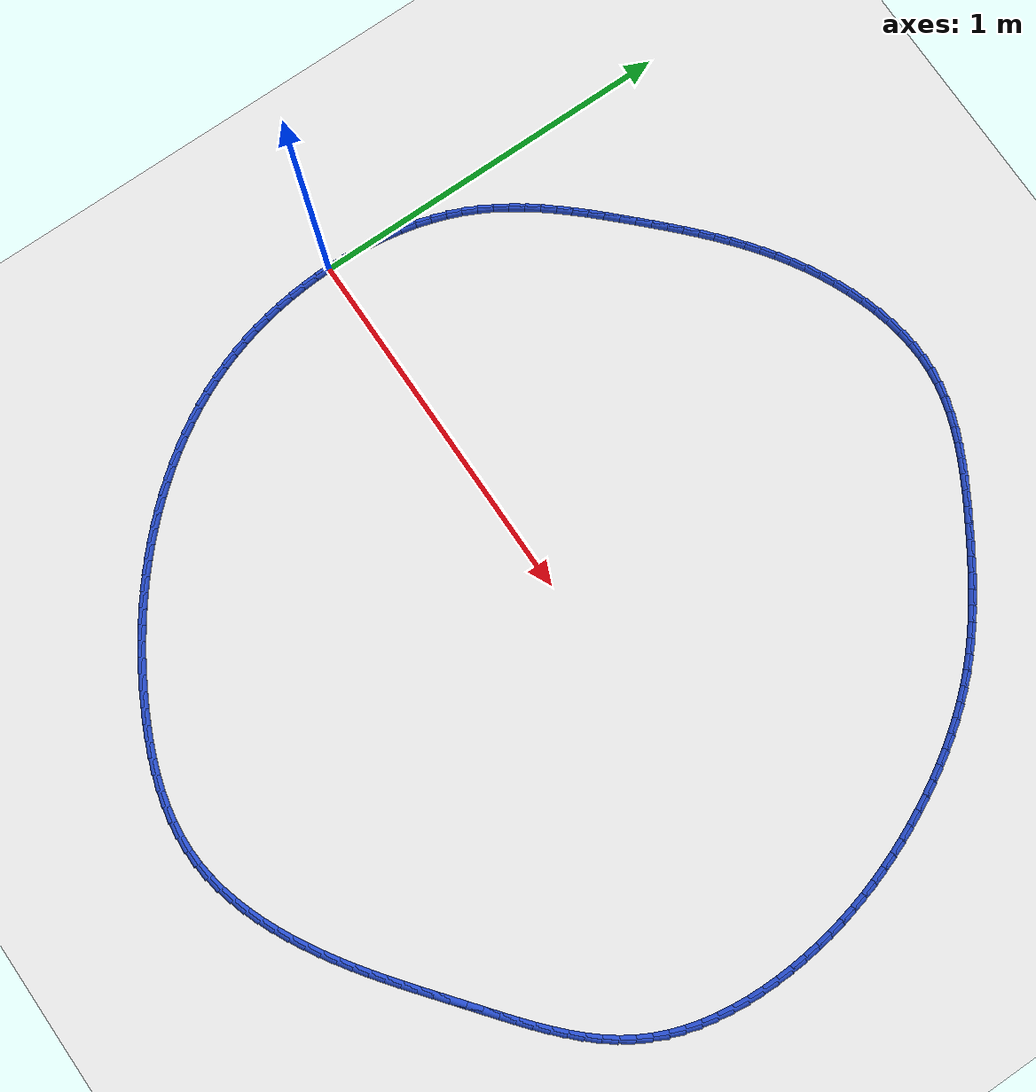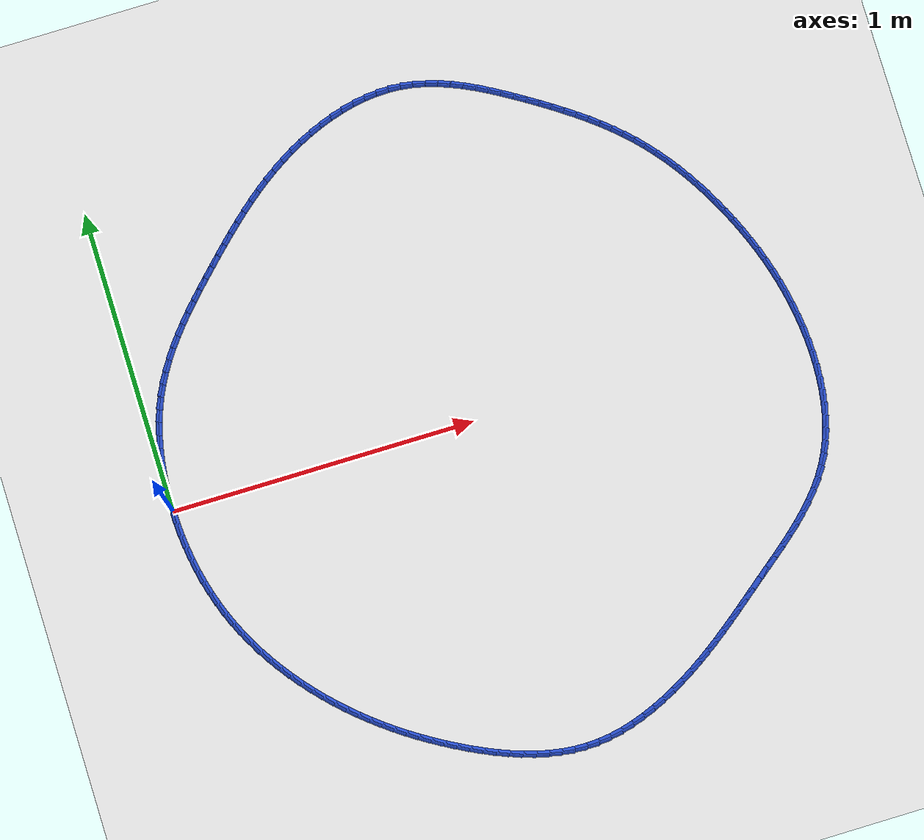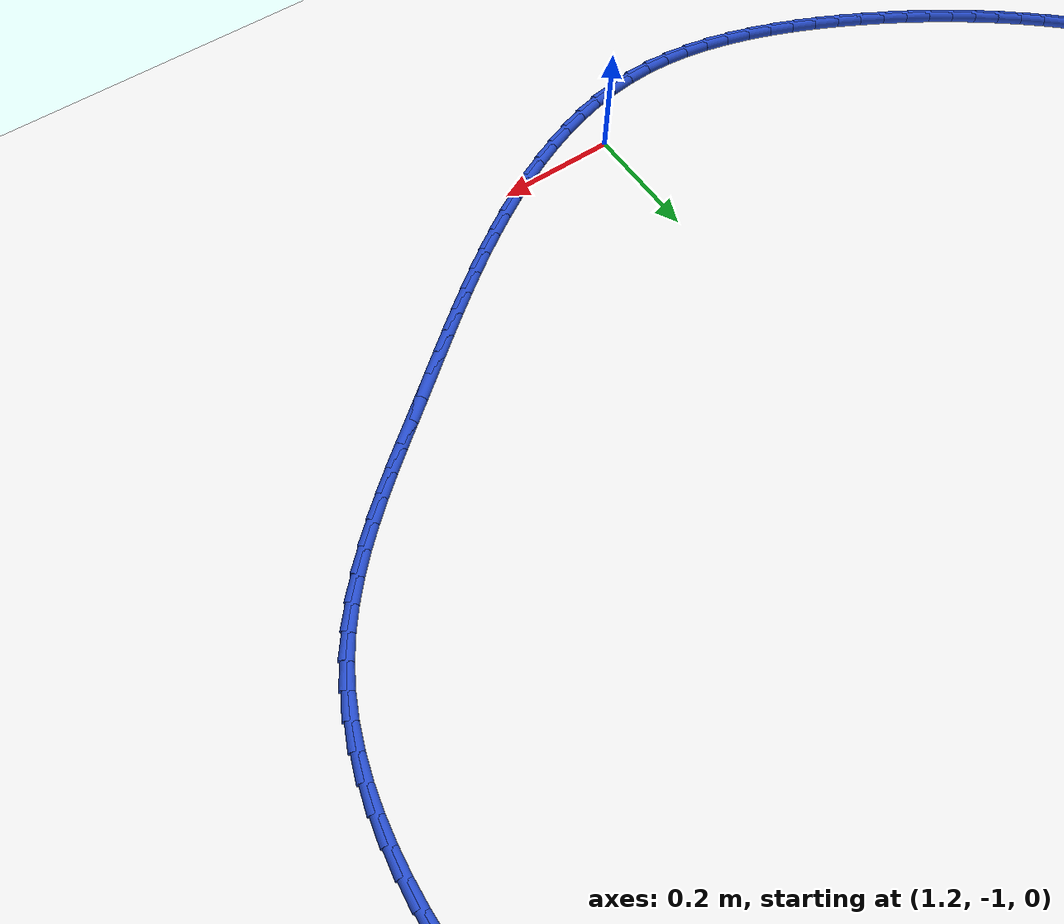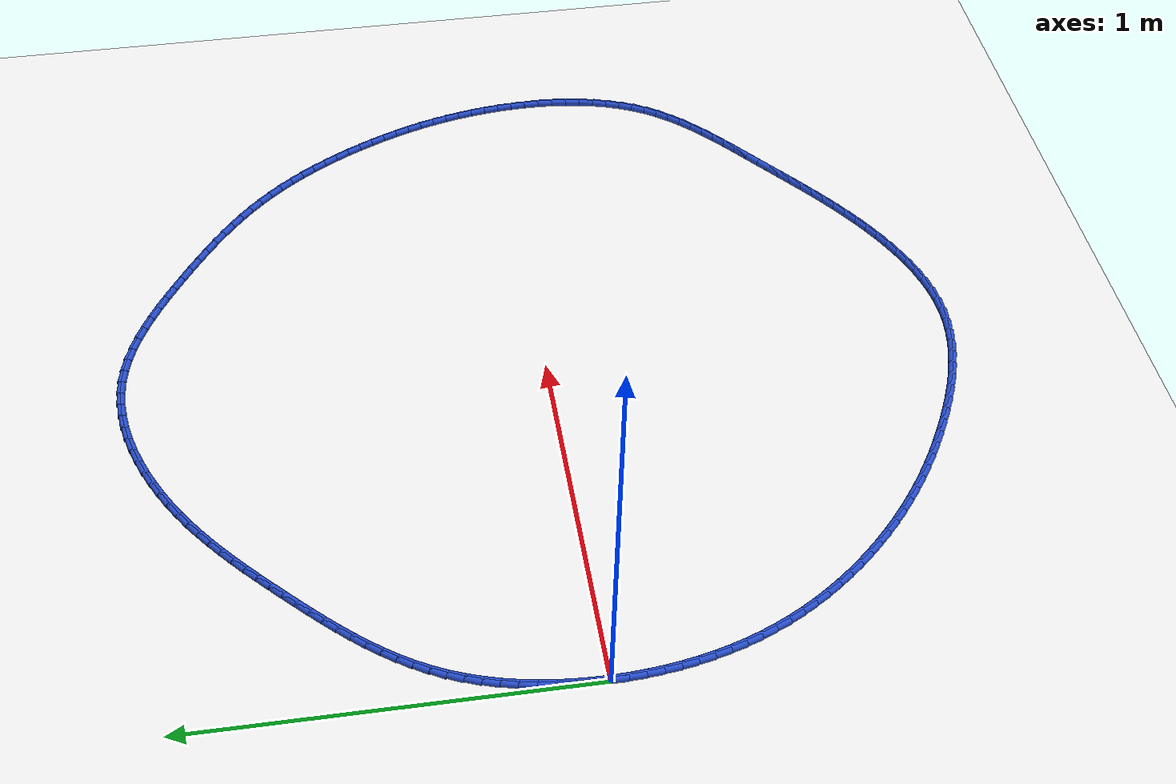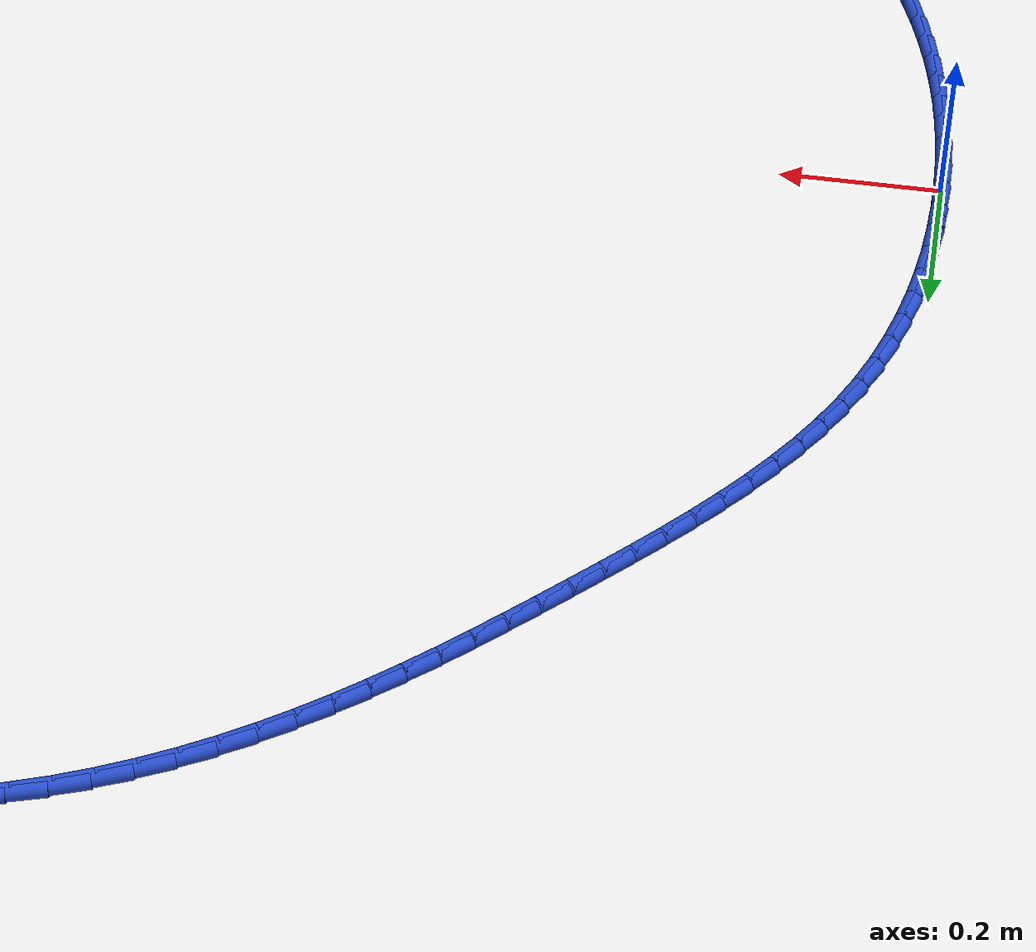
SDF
<sdf version="1.6">
 <world name="default">
  <light name="sun" type="directional">
   <pose>0 0 10 0 -0 0</pose>
   <diffuse>0.8 0.8 0.8 1</diffuse>
   <specular>0.2 0.2 0.2 1</specular>
   <attenuation>
    <range>1000</range>
    <constant>0.9</constant>
    <linear>0.01</linear>
    <quadratic>0.001</quadratic>
   </attenuation>
   <direction>-0.5 0.1 -0.9</direction>
  </light>
  <model name="ground_plane">
   <static>1</static>
   <link name="link">
    <collision name="collision">
     <geometry><plane><normal>0 0 1</normal><size>100 100</size></plane></geometry>
     <surface><friction><ode><mu>100</mu><mu2>50</mu2></ode></friction></surface>
    </collision>
    <visual name="visual">
     <cast_shadows>0</cast_shadows>
     <geometry><plane><normal>0 0 1</normal><size>100 100</size></plane></geometry>
     <material>
      <script><uri>file://media/materials/scripts/gazebo.material</uri><name>Gazebo/WhiteGlow</name></script>
     </material>
    </visual>
   </link>
  </model>
  <gravity>0 0 -9.8</gravity>
  <magnetic_field>6e-06 2.3e-05 -4.2e-05</magnetic_field>
  <atmosphere type="adiabatic"/>
  <physics name="default_physics" default="0" type="ode">
   <max_step_size>0.001</max_step_size>
   <real_time_factor>1</real_time_factor>
   <real_time_update_rate>1000</real_time_update_rate>
  </physics>
  <scene><ambient>0.4 0.4 0.4 1</ambient><background>0.7 0.7 0.7 1</background><shadows>1</shadows></scene>
  <spherical_coordinates>
   <surface_model>EARTH_WGS84</surface_model>
   <latitude_deg>0</latitude_deg>
   <longitude_deg>0</longitude_deg>
   <elevation>0</elevation>
   <heading_deg>0</heading_deg>
  </spherical_coordinates>
  <model name="line">
   <link name="link_0">
    <pose>5.204170427930421e-18 1.3877787807814457e-17 0.01 0 1.57 1.5624504358657028</pose>
    <collision name="collision">
     <geometry><cylinder><radius>0.01</radius><length>0.08</length></cylinder></geometry>
    </collision>
    <visual name="visual">
     <material>
      <script><name>Gazebo/Blue</name><uri>file://media/materials/scripts/gazebo.material</uri></script>
     </material>
     <geometry><cylinder><radius>0.01</radius><length>0.08</length></cylinder></geometry>
    </visual>
   </link>
   <link name="link_1">
    <pose>0.0003475301557996371 0.04163990276981557 0.01 0 1.57 1.5242031196906132</pose>
    <collision name="collision">
     <geometry><cylinder><radius>0.01</radius><length>0.08</length></cylinder></geometry>
    </collision>
    <visual name="visual">
     <material>
      <script><name>Gazebo/Blue</name><uri>file://media/materials/scripts/gazebo.material</uri></script>
     </material>
     <geometry><cylinder><radius>0.01</radius><length>0.08</length></cylinder></geometry>
    </visual>
   </link>
   <link name="link_2">
    <pose>0.002288513042845296 0.08326781865953595 0.01 0 1.57 1.4839324796471192</pose>
    <collision name="collision">
     <geometry><cylinder><radius>0.01</radius><length>0.08</length></cylinder></geometry>
    </collision>
    <visual name="visual">
     <material>
      <script><name>Gazebo/Blue</name><uri>file://media/materials/scripts/gazebo.material</uri></script>
     </material>
     <geometry><cylinder><radius>0.01</radius><length>0.08</length></cylinder></geometry>
    </visual>
   </link>
   <link name="link_3">
    <pose>0.005900698818099135 0.12474763193301873 0.01 0 1.57 1.4413849862954236</pose>
    <collision name="collision">
     <geometry><cylinder><radius>0.01</radius><length>0.08</length></cylinder></geometry>
    </collision>
    <visual name="visual">
     <material>
      <script><name>Gazebo/Blue</name><uri>file://media/materials/scripts/gazebo.material</uri></script>
     </material>
     <geometry><cylinder><radius>0.01</radius><length>0.08</length></cylinder></geometry>
    </visual>
   </link>
   <link name="link_4">
    <pose>0.01126183763852328 0.16594322685412136 0.01 0 1.57 1.3963094645022793</pose>
    <collision name="collision">
     <geometry><cylinder><radius>0.01</radius><length>0.08</length></cylinder></geometry>
    </collision>
    <visual name="visual">
     <material>
      <script><name>Gazebo/Blue</name><uri>file://media/materials/scripts/gazebo.material</uri></script>
     </material>
     <geometry><cylinder><radius>0.01</radius><length>0.08</length></cylinder></geometry>
    </visual>
   </link>
   <link name="link_5">
    <pose>0.018449679661079885 0.2067184876867016 0.01 0 1.57 1.348462995993757</pose>
    <collision name="collision">
     <geometry><cylinder><radius>0.01</radius><length>0.08</length></cylinder></geometry>
    </collision>
    <visual name="visual">
     <material>
      <script><name>Gazebo/Blue</name><uri>file://media/materials/scripts/gazebo.material</uri></script>
     </material>
     <geometry><cylinder><radius>0.01</radius><length>0.08</length></cylinder></geometry>
    </visual>
   </link>
   <link name="link_6">
    <pose>0.027541975042731107 0.2469372986946169 0.01 0 1.57 1.2976198860110693</pose>
    <collision name="collision">
     <geometry><cylinder><radius>0.01</radius><length>0.08</length></cylinder></geometry>
    </collision>
    <visual name="visual">
     <material>
      <script><name>Gazebo/Blue</name><uri>file://media/materials/scripts/gazebo.material</uri></script>
     </material>
     <geometry><cylinder><radius>0.01</radius><length>0.08</length></cylinder></geometry>
    </visual>
   </link>
   <link name="link_7">
    <pose>0.03861647394043905 0.28646354414172476 0.01 0 1.57 1.2435841757331088</pose>
    <collision name="collision">
     <geometry><cylinder><radius>0.01</radius><length>0.08</length></cylinder></geometry>
    </collision>
    <visual name="visual">
     <material>
      <script><name>Gazebo/Blue</name><uri>file://media/materials/scripts/gazebo.material</uri></script>
     </material>
     <geometry><cylinder><radius>0.01</radius><length>0.08</length></cylinder></geometry>
    </visual>
   </link>
   <link name="link_8">
    <pose>0.051750926511165876 0.3251611082918828 0.01 0 1.57 1.1862059646722516</pose>
    <collision name="collision">
     <geometry><cylinder><radius>0.01</radius><length>0.08</length></cylinder></geometry>
    </collision>
    <visual name="visual">
     <material>
      <script><name>Gazebo/Blue</name><uri>file://media/materials/scripts/gazebo.material</uri></script>
     </material>
     <geometry><cylinder><radius>0.01</radius><length>0.08</length></cylinder></geometry>
    </visual>
   </link>
   <link name="link_9">
    <pose>0.06702308291187374 0.3628938754089487 0.01 0 1.57 1.125550118626905</pose>
    <collision name="collision">
     <geometry><cylinder><radius>0.01</radius><length>0.08</length></cylinder></geometry>
    </collision>
    <visual name="visual">
     <material>
      <script><name>Gazebo/Blue</name><uri>file://media/materials/scripts/gazebo.material</uri></script>
     </material>
     <geometry><cylinder><radius>0.01</radius><length>0.08</length></cylinder></geometry>
    </visual>
   </link>
   <link name="link_10">
    <pose>0.08450578518327874 0.39952946709786913 0.01 0 1.57 1.0657579596768623</pose>
    <collision name="collision">
     <geometry><cylinder><radius>0.01</radius><length>0.08</length></cylinder></geometry>
    </collision>
    <visual name="visual">
     <material>
      <script><name>Gazebo/Blue</name><uri>file://media/materials/scripts/gazebo.material</uri></script>
     </material>
     <geometry><cylinder><radius>0.01</radius><length>0.08</length></cylinder></geometry>
    </visual>
   </link>
   <link name="link_11">
    <pose>0.10413716993710452 0.43503807794872323 0.01 0 1.57 1.0115760830622713</pose>
    <collision name="collision">
     <geometry><cylinder><radius>0.01</radius><length>0.08</length></cylinder></geometry>
    </collision>
    <visual name="visual">
     <material>
      <script><name>Gazebo/Blue</name><uri>file://media/materials/scripts/gazebo.material</uri></script>
     </material>
     <geometry><cylinder><radius>0.01</radius><length>0.08</length></cylinder></geometry>
    </visual>
   </link>
   <link name="link_12">
    <pose>0.12570730107626843 0.469502654204381 0.01 0 1.57 0.9633854211569818</pose>
    <collision name="collision">
     <geometry><cylinder><radius>0.01</radius><length>0.08</length></cylinder></geometry>
    </collision>
    <visual name="visual">
     <material>
      <script><name>Gazebo/Blue</name><uri>file://media/materials/scripts/gazebo.material</uri></script>
     </material>
     <geometry><cylinder><radius>0.01</radius><length>0.08</length></cylinder></geometry>
    </visual>
   </link>
   <link name="link_13">
    <pose>0.14899865342710944 0.503011920896621 0.01 0 1.57 0.9211859444674497</pose>
    <collision name="collision">
     <geometry><cylinder><radius>0.01</radius><length>0.08</length></cylinder></geometry>
    </collision>
    <visual name="visual">
     <material>
      <script><name>Gazebo/Blue</name><uri>file://media/materials/scripts/gazebo.material</uri></script>
     </material>
     <geometry><cylinder><radius>0.01</radius><length>0.08</length></cylinder></geometry>
    </visual>
   </link>
   <link name="link_14">
    <pose>0.1737937018159669 0.5356546030572222 0.01 0 1.57 0.8848788467114191</pose>
    <collision name="collision">
     <geometry><cylinder><radius>0.01</radius><length>0.08</length></cylinder></geometry>
    </collision>
    <visual name="visual">
     <material>
      <script><name>Gazebo/Blue</name><uri>file://media/materials/scripts/gazebo.material</uri></script>
     </material>
     <geometry><cylinder><radius>0.01</radius><length>0.08</length></cylinder></geometry>
    </visual>
   </link>
   <link name="link_15">
    <pose>0.19987492106917987 0.5675194257179637 0.01 0 1.57 0.8543121804191491</pose>
    <collision name="collision">
     <geometry><cylinder><radius>0.01</radius><length>0.08</length></cylinder></geometry>
    </collision>
    <visual name="visual">
     <material>
      <script><name>Gazebo/Blue</name><uri>file://media/materials/scripts/gazebo.material</uri></script>
     </material>
     <geometry><cylinder><radius>0.01</radius><length>0.08</length></cylinder></geometry>
    </visual>
   </link>
   <link name="link_16">
    <pose>0.22702478601308754 0.5986951139106239 0.01 0 1.57 0.8293176231968055</pose>
    <collision name="collision">
     <geometry><cylinder><radius>0.01</radius><length>0.08</length></cylinder></geometry>
    </collision>
    <visual name="visual">
     <material>
      <script><name>Gazebo/Blue</name><uri>file://media/materials/scripts/gazebo.material</uri></script>
     </material>
     <geometry><cylinder><radius>0.01</radius><length>0.08</length></cylinder></geometry>
    </visual>
   </link>
   <link name="link_17">
    <pose>0.255025771474029 0.6292703926669819 0.01 0 1.57 0.8097384657332911</pose>
    <collision name="collision">
     <geometry><cylinder><radius>0.01</radius><length>0.08</length></cylinder></geometry>
    </collision>
    <visual name="visual">
     <material>
      <script><name>Gazebo/Blue</name><uri>file://media/materials/scripts/gazebo.material</uri></script>
     </material>
     <geometry><cylinder><radius>0.01</radius><length>0.08</length></cylinder></geometry>
    </visual>
   </link>
   <link name="link_18">
    <pose>0.28366035227834346 0.6593339870188163 0.01 0 1.57 0.7954501519371617</pose>
    <collision name="collision">
     <geometry><cylinder><radius>0.01</radius><length>0.08</length></cylinder></geometry>
    </collision>
    <visual name="visual">
     <material>
      <script><name>Gazebo/Blue</name><uri>file://media/materials/scripts/gazebo.material</uri></script>
     </material>
     <geometry><cylinder><radius>0.01</radius><length>0.08</length></cylinder></geometry>
    </visual>
   </link>
   <link name="link_19">
    <pose>0.31271100325237017 0.6889746219979064 0.01 0 1.57 0.7863750864269589</pose>
    <collision name="collision">
     <geometry><cylinder><radius>0.01</radius><length>0.08</length></cylinder></geometry>
    </collision>
    <visual name="visual">
     <material>
      <script><name>Gazebo/Blue</name><uri>file://media/materials/scripts/gazebo.material</uri></script>
     </material>
     <geometry><cylinder><radius>0.01</radius><length>0.08</length></cylinder></geometry>
    </visual>
   </link>
   <link name="link_20">
    <pose>0.3419601994428889 0.7182810225175562 0.01 0 1.57 0.7809129598063201</pose>
    <collision name="collision">
     <geometry><cylinder><radius>0.01</radius><length>0.08</length></cylinder></geometry>
    </collision>
    <visual name="visual">
     <material>
      <script><name>Gazebo/Blue</name><uri>file://media/materials/scripts/gazebo.material</uri></script>
     </material>
     <geometry><cylinder><radius>0.01</radius><length>0.08</length></cylinder></geometry>
    </visual>
   </link>
   <link name="link_21">
    <pose>0.37125041706443196 0.7473096664179376 0.01 0 1.57 0.7730311262923875</pose>
    <collision name="collision">
     <geometry><cylinder><radius>0.01</radius><length>0.08</length></cylinder></geometry>
    </collision>
    <visual name="visual">
     <material>
      <script><name>Gazebo/Blue</name><uri>file://media/materials/scripts/gazebo.material</uri></script>
     </material>
     <geometry><cylinder><radius>0.01</radius><length>0.08</length></cylinder></geometry>
    </visual>
   </link>
   <link name="link_22">
    <pose>0.40065311712629853 0.7759939657773348 0.01 0 1.57 0.7612646481107757</pose>
    <collision name="collision">
     <geometry><cylinder><radius>0.01</radius><length>0.08</length></cylinder></geometry>
    </collision>
    <visual name="visual">
     <material>
      <script><name>Gazebo/Blue</name><uri>file://media/materials/scripts/gazebo.material</uri></script>
     </material>
     <geometry><cylinder><radius>0.01</radius><length>0.08</length></cylinder></geometry>
    </visual>
   </link>
   <link name="link_23">
    <pose>0.4302943772468943 0.8042379794821831 0.01 0 1.57 0.7456000215260823</pose>
    <collision name="collision">
     <geometry><cylinder><radius>0.01</radius><length>0.08</length></cylinder></geometry>
    </collision>
    <visual name="visual">
     <material>
      <script><name>Gazebo/Blue</name><uri>file://media/materials/scripts/gazebo.material</uri></script>
     </material>
     <geometry><cylinder><radius>0.01</radius><length>0.08</length></cylinder></geometry>
    </visual>
   </link>
   <link name="link_24">
    <pose>0.4603002750446251 0.8319457664189187 0.01 0 1.57 0.7260470476379888</pose>
    <collision name="collision">
     <geometry><cylinder><radius>0.01</radius><length>0.08</length></cylinder></geometry>
    </collision>
    <visual name="visual">
     <material>
      <script><name>Gazebo/Blue</name><uri>file://media/materials/scripts/gazebo.material</uri></script>
     </material>
     <geometry><cylinder><radius>0.01</radius><length>0.08</length></cylinder></geometry>
    </visual>
   </link>
   <link name="link_25">
    <pose>0.49079688813789646 0.859021385473977 0.01 0 1.57 0.702646051335076</pose>
    <collision name="collision">
     <geometry><cylinder><radius>0.01</radius><length>0.08</length></cylinder></geometry>
    </collision>
    <visual name="visual">
     <material>
      <script><name>Gazebo/Blue</name><uri>file://media/materials/scripts/gazebo.material</uri></script>
     </material>
     <geometry><cylinder><radius>0.01</radius><length>0.08</length></cylinder></geometry>
    </visual>
   </link>
   <link name="link_26">
    <pose>0.5219102941451139 0.8853688955337938 0.01 0 1.57 0.675476258908503</pose>
    <collision name="collision">
     <geometry><cylinder><radius>0.01</radius><length>0.08</length></cylinder></geometry>
    </collision>
    <visual name="visual">
     <material>
      <script><name>Gazebo/Blue</name><uri>file://media/materials/scripts/gazebo.material</uri></script>
     </material>
     <geometry><cylinder><radius>0.01</radius><length>0.08</length></cylinder></geometry>
    </visual>
   </link>
   <link name="link_27">
    <pose>0.5537665706846829 0.9108923554848045 0.01 0 1.57 0.6446647022555019</pose>
    <collision name="collision">
     <geometry><cylinder><radius>0.01</radius><length>0.08</length></cylinder></geometry>
    </collision>
    <visual name="visual">
     <material>
      <script><name>Gazebo/Blue</name><uri>file://media/materials/scripts/gazebo.material</uri></script>
     </material>
     <geometry><cylinder><radius>0.01</radius><length>0.08</length></cylinder></geometry>
    </visual>
   </link>
   <link name="link_28">
    <pose>0.5864917953750094 0.935495824213445 0.01 0 1.57 0.6103947196575686</pose>
    <collision name="collision">
     <geometry><cylinder><radius>0.01</radius><length>0.08</length></cylinder></geometry>
    </collision>
    <visual name="visual">
     <material>
      <script><name>Gazebo/Blue</name><uri>file://media/materials/scripts/gazebo.material</uri></script>
     </material>
     <geometry><cylinder><radius>0.01</radius><length>0.08</length></cylinder></geometry>
    </visual>
   </link>
   <link name="link_29">
    <pose>0.6202120458344988 0.9590833606061511 0.01 0 1.57 0.5729128440158021</pose>
    <collision name="collision">
     <geometry><cylinder><radius>0.01</radius><length>0.08</length></cylinder></geometry>
    </collision>
    <visual name="visual">
     <material>
      <script><name>Gazebo/Blue</name><uri>file://media/materials/scripts/gazebo.material</uri></script>
     </material>
     <geometry><cylinder><radius>0.01</radius><length>0.08</length></cylinder></geometry>
    </visual>
   </link>
   <link name="link_30">
    <pose>0.6550533996815568 0.9815590235493583 0.01 0 1.57 0.5326235998862437</pose>
    <collision name="collision">
     <geometry><cylinder><radius>0.01</radius><length>0.08</length></cylinder></geometry>
    </collision>
    <visual name="visual">
     <material>
      <script><name>Gazebo/Blue</name><uri>file://media/materials/scripts/gazebo.material</uri></script>
     </material>
     <geometry><cylinder><radius>0.01</radius><length>0.08</length></cylinder></geometry>
    </visual>
   </link>
   <link name="link_31">
    <pose>0.6911198886534237 1.002818297357844 0.01 0 1.57 0.49037305305525103</pose>
    <collision name="collision">
     <geometry><cylinder><radius>0.01</radius><length>0.08</length></cylinder></geometry>
    </collision>
    <visual name="visual">
     <material>
      <script><name>Gazebo/Blue</name><uri>file://media/materials/scripts/gazebo.material</uri></script>
     </material>
     <geometry><cylinder><radius>0.01</radius><length>0.08</length></cylinder></geometry>
    </visual>
   </link>
   <link name="link_32">
    <pose>0.728336461378059 1.0226870133830108 0.01 0 1.57 0.4460712215297842</pose>
    <collision name="collision">
     <geometry><cylinder><radius>0.01</radius><length>0.08</length></cylinder></geometry>
    </collision>
    <visual name="visual">
     <material>
      <script><name>Gazebo/Blue</name><uri>file://media/materials/scripts/gazebo.material</uri></script>
     </material>
     <geometry><cylinder><radius>0.01</radius><length>0.08</length></cylinder></geometry>
    </visual>
   </link>
   <link name="link_33">
    <pose>0.7665410147893905 1.0409571449062278 0.01 0 1.57 0.3991680516487144</pose>
    <collision name="collision">
     <geometry><cylinder><radius>0.01</radius><length>0.08</length></cylinder></geometry>
    </collision>
    <visual name="visual">
     <material>
      <script><name>Gazebo/Blue</name><uri>file://media/materials/scripts/gazebo.material</uri></script>
     </material>
     <geometry><cylinder><radius>0.01</radius><length>0.08</length></cylinder></geometry>
    </visual>
   </link>
   <link name="link_34">
    <pose>0.8055708668792918 1.0574204400339158 0.01 0 1.57 0.34909543104826807</pose>
    <collision name="collision">
     <geometry><cylinder><radius>0.01</radius><length>0.08</length></cylinder></geometry>
    </collision>
    <visual name="visual">
     <material>
      <script><name>Gazebo/Blue</name><uri>file://media/materials/scripts/gazebo.material</uri></script>
     </material>
     <geometry><cylinder><radius>0.01</radius><length>0.08</length></cylinder></geometry>
    </visual>
   </link>
   <link name="link_35">
    <pose>0.8452633356396357 1.0718686468724954 0.01 0 1.57 0.29526767775291624</pose>
    <collision name="collision">
     <geometry><cylinder><radius>0.01</radius><length>0.08</length></cylinder></geometry>
    </collision>
    <visual name="visual">
     <material>
      <script><name>Gazebo/Blue</name><uri>file://media/materials/scripts/gazebo.material</uri></script>
     </material>
     <geometry><cylinder><radius>0.01</radius><length>0.08</length></cylinder></geometry>
    </visual>
   </link>
   <link name="link_36">
    <pose>0.8854557390622957 1.0840935135283878 0.01 0 1.57 0.23708782129753006</pose>
    <collision name="collision">
     <geometry><cylinder><radius>0.01</radius><length>0.08</length></cylinder></geometry>
    </collision>
    <visual name="visual">
     <material>
      <script><name>Gazebo/Blue</name><uri>file://media/materials/scripts/gazebo.material</uri></script>
     </material>
     <geometry><cylinder><radius>0.01</radius><length>0.08</length></cylinder></geometry>
    </visual>
   </link>
   <link name="link_37">
    <pose>0.9259853951391442 1.0938867881080137 0.01 0 1.57 0.17396525060231066</pose>
    <collision name="collision">
     <geometry><cylinder><radius>0.01</radius><length>0.08</length></cylinder></geometry>
    </collision>
    <visual name="visual">
     <material>
      <script><name>Gazebo/Blue</name><uri>file://media/materials/scripts/gazebo.material</uri></script>
     </material>
     <geometry><cylinder><radius>0.01</radius><length>0.08</length></cylinder></geometry>
    </visual>
   </link>
   <link name="link_38">
    <pose>0.9666896218620546 1.1010402187177943 0.01 0 1.57 0.10534884038553156</pose>
    <collision name="collision">
     <geometry><cylinder><radius>0.01</radius><length>0.08</length></cylinder></geometry>
    </collision>
    <visual name="visual">
     <material>
      <script><name>Gazebo/Blue</name><uri>file://media/materials/scripts/gazebo.material</uri></script>
     </material>
     <geometry><cylinder><radius>0.01</radius><length>0.08</length></cylinder></geometry>
    </visual>
   </link>
   <link name="link_39">
    <pose>1.0074057372229 1.1053455534641503 0.01 0 1.57 0.03077980094029954</pose>
    <collision name="collision">
     <geometry><cylinder><radius>0.01</radius><length>0.08</length></cylinder></geometry>
    </collision>
    <visual name="visual">
     <material>
      <script><name>Gazebo/Blue</name><uri>file://media/materials/scripts/gazebo.material</uri></script>
     </material>
     <geometry><cylinder><radius>0.01</radius><length>0.08</length></cylinder></geometry>
    </visual>
   </link>
   <link name="link_40">
    <pose>1.0479710592135532 1.1065945404535027 0.01 0 1.57 -0.05003324414728387</pose>
    <collision name="collision">
     <geometry><cylinder><radius>0.01</radius><length>0.08</length></cylinder></geometry>
    </collision>
    <visual name="visual">
     <material>
      <script><name>Gazebo/Blue</name><uri>file://media/materials/scripts/gazebo.material</uri></script>
     </material>
     <geometry><cylinder><radius>0.01</radius><length>0.08</length></cylinder></geometry>
    </visual>
   </link>
   <link name="link_41">
    <pose>1.0882229058258879 1.1045789277922726 0.01 0 1.57 -0.13553702553732105</pose>
    <collision name="collision">
     <geometry><cylinder><radius>0.01</radius><length>0.08</length></cylinder></geometry>
    </collision>
    <visual name="visual">
     <material>
      <script><name>Gazebo/Blue</name><uri>file://media/materials/scripts/gazebo.material</uri></script>
     </material>
     <geometry><cylinder><radius>0.01</radius><length>0.08</length></cylinder></geometry>
    </visual>
   </link>
   <link name="link_42">
    <pose>1.128017947864307 1.0991519537061352 0.01 0 1.57 -0.2161667827833196</pose>
    <collision name="collision">
     <geometry><cylinder><radius>0.01</radius><length>0.08</length></cylinder></geometry>
    </collision>
    <visual name="visual">
     <material>
      <script><name>Gazebo/Blue</name><uri>file://media/materials/scripts/gazebo.material</uri></script>
     </material>
     <geometry><cylinder><radius>0.01</radius><length>0.08</length></cylinder></geometry>
    </visual>
   </link>
   <link name="link_43">
    <pose>1.1673241262843495 1.0905203975327749 0.01 0 1.57 -0.28804515740071235</pose>
    <collision name="collision">
     <geometry><cylinder><radius>0.01</radius><length>0.08</length></cylinder></geometry>
    </collision>
    <visual name="visual">
     <material>
      <script><name>Gazebo/Blue</name><uri>file://media/materials/scripts/gazebo.material</uri></script>
     </material>
     <geometry><cylinder><radius>0.01</radius><length>0.08</length></cylinder></geometry>
    </visual>
   </link>
   <link name="link_44">
    <pose>1.2061490714492047 1.0790171446425618 0.01 0 1.57 -0.35097885810257234</pose>
    <collision name="collision">
     <geometry><cylinder><radius>0.01</radius><length>0.08</length></cylinder></geometry>
    </collision>
    <visual name="visual">
     <material>
      <script><name>Gazebo/Blue</name><uri>file://media/materials/scripts/gazebo.material</uri></script>
     </material>
     <geometry><cylinder><radius>0.01</radius><length>0.08</length></cylinder></geometry>
    </visual>
   </link>
   <link name="link_45">
    <pose>1.2445004627230363 1.0649752360977507 0.01 0 1.57 -0.4051342257002281</pose>
    <collision name="collision">
     <geometry><cylinder><radius>0.01</radius><length>0.08</length></cylinder></geometry>
    </collision>
    <visual name="visual">
     <material>
      <script><name>Gazebo/Blue</name><uri>file://media/materials/scripts/gazebo.material</uri></script>
     </material>
     <geometry><cylinder><radius>0.01</radius><length>0.08</length></cylinder></geometry>
    </visual>
   </link>
   <link name="link_46">
    <pose>1.28238597947001 1.0487277129605947 0.01 0 1.57 -0.45088001485626605</pose>
    <collision name="collision">
     <geometry><cylinder><radius>0.01</radius><length>0.08</length></cylinder></geometry>
    </collision>
    <visual name="visual">
     <material>
      <script><name>Gazebo/Blue</name><uri>file://media/materials/scripts/gazebo.material</uri></script>
     </material>
     <geometry><cylinder><radius>0.01</radius><length>0.08</length></cylinder></geometry>
    </visual>
   </link>
   <link name="link_47">
    <pose>1.31981330105429 1.030607616293349 0.01 0 1.57 -0.48866505048923775</pose>
    <collision name="collision">
     <geometry><cylinder><radius>0.01</radius><length>0.08</length></cylinder></geometry>
    </collision>
    <visual name="visual">
     <material>
      <script><name>Gazebo/Blue</name><uri>file://media/materials/scripts/gazebo.material</uri></script>
     </material>
     <geometry><cylinder><radius>0.01</radius><length>0.08</length></cylinder></geometry>
    </visual>
   </link>
   <link name="link_48">
    <pose>1.3567901068400412 1.0109479871582665 0.01 0 1.57 -0.5189308043068782</pose>
    <collision name="collision">
     <geometry><cylinder><radius>0.01</radius><length>0.08</length></cylinder></geometry>
    </collision>
    <visual name="visual">
     <material>
      <script><name>Gazebo/Blue</name><uri>file://media/materials/scripts/gazebo.material</uri></script>
     </material>
     <geometry><cylinder><radius>0.01</radius><length>0.08</length></cylinder></geometry>
    </visual>
   </link>
   <link name="link_49">
    <pose>1.3933240761914285 0.990081866617602 0.01 0 1.57 -0.542053185050808</pose>
    <collision name="collision">
     <geometry><cylinder><radius>0.01</radius><length>0.08</length></cylinder></geometry>
    </collision>
    <visual name="visual">
     <material>
      <script><name>Gazebo/Blue</name><uri>file://media/materials/scripts/gazebo.material</uri></script>
     </material>
     <geometry><cylinder><radius>0.01</radius><length>0.08</length></cylinder></geometry>
    </visual>
   </link>
   <link name="link_50">
    <pose>1.429422888472616 0.968342295733609 0.01 0 1.57 -0.558304859155313</pose>
    <collision name="collision">
     <geometry><cylinder><radius>0.01</radius><length>0.08</length></cylinder></geometry>
    </collision>
    <visual name="visual">
     <material>
      <script><name>Gazebo/Blue</name><uri>file://media/materials/scripts/gazebo.material</uri></script>
     </material>
     <geometry><cylinder><radius>0.01</radius><length>0.08</length></cylinder></geometry>
    </visual>
   </link>
   <link name="link_51">
    <pose>1.465094223047769 0.9460623155685401 0.01 0 1.57 -0.5695343102827728</pose>
    <collision name="collision">
     <geometry><cylinder><radius>0.01</radius><length>0.08</length></cylinder></geometry>
    </collision>
    <visual name="visual">
     <material>
      <script><name>Gazebo/Blue</name><uri>file://media/materials/scripts/gazebo.material</uri></script>
     </material>
     <geometry><cylinder><radius>0.01</radius><length>0.08</length></cylinder></geometry>
    </visual>
   </link>
   <link name="link_52">
    <pose>1.5003308390457684 0.9234998968884501 0.01 0 1.57 -0.5826063062580944</pose>
    <collision name="collision">
     <geometry><cylinder><radius>0.01</radius><length>0.08</length></cylinder></geometry>
    </collision>
    <visual name="visual">
     <material>
      <script><name>Gazebo/Blue</name><uri>file://media/materials/scripts/gazebo.material</uri></script>
     </material>
     <geometry><cylinder><radius>0.01</radius><length>0.08</length></cylinder></geometry>
    </visual>
   </link>
   <link name="link_53">
    <pose>1.535065866729008 0.900612991285142 0.01 0 1.57 -0.599280844746613</pose>
    <collision name="collision">
     <geometry><cylinder><radius>0.01</radius><length>0.08</length></cylinder></geometry>
    </collision>
    <visual name="visual">
     <material>
      <script><name>Gazebo/Blue</name><uri>file://media/materials/scripts/gazebo.material</uri></script>
     </material>
     <geometry><cylinder><radius>0.01</radius><length>0.08</length></cylinder></geometry>
    </visual>
   </link>
   <link name="link_54">
    <pose>1.5692175421505619 0.8772846110023468 0.01 0 1.57 -0.619613896667951</pose>
    <collision name="collision">
     <geometry><cylinder><radius>0.01</radius><length>0.08</length></cylinder></geometry>
    </collision>
    <visual name="visual">
     <material>
      <script><name>Gazebo/Blue</name><uri>file://media/materials/scripts/gazebo.material</uri></script>
     </material>
     <geometry><cylinder><radius>0.01</radius><length>0.08</length></cylinder></geometry>
    </visual>
   </link>
   <link name="link_55">
    <pose>1.602704101363506 0.8533977682837962 0.01 0 1.57 -0.6436483607772273</pose>
    <collision name="collision">
     <geometry><cylinder><radius>0.01</radius><length>0.08</length></cylinder></geometry>
    </collision>
    <visual name="visual">
     <material>
      <script><name>Gazebo/Blue</name><uri>file://media/materials/scripts/gazebo.material</uri></script>
     </material>
     <geometry><cylinder><radius>0.01</radius><length>0.08</length></cylinder></geometry>
    </visual>
   </link>
   <link name="link_56">
    <pose>1.6354437804209143 0.8288354753732197 0.01 0 1.57 -0.6714054299900848</pose>
    <collision name="collision">
     <geometry><cylinder><radius>0.01</radius><length>0.08</length></cylinder></geometry>
    </collision>
    <visual name="visual">
     <material>
      <script><name>Gazebo/Blue</name><uri>file://media/materials/scripts/gazebo.material</uri></script>
     </material>
     <geometry><cylinder><radius>0.01</radius><length>0.08</length></cylinder></geometry>
    </visual>
   </link>
   <link name="link_57">
    <pose>1.6673548153758617 0.8034807445143493 0.01 0 1.57 -0.7028742616804411</pose>
    <collision name="collision">
     <geometry><cylinder><radius>0.01</radius><length>0.08</length></cylinder></geometry>
    </collision>
    <visual name="visual">
     <material>
      <script><name>Gazebo/Blue</name><uri>file://media/materials/scripts/gazebo.material</uri></script>
     </material>
     <geometry><cylinder><radius>0.01</radius><length>0.08</length></cylinder></geometry>
    </visual>
   </link>
   <link name="link_58">
    <pose>1.6983554422814235 0.7772165879509153 0.01 0 1.57 -0.7380003360959638</pose>
    <collision name="collision">
     <geometry><cylinder><radius>0.01</radius><length>0.08</length></cylinder></geometry>
    </collision>
    <visual name="visual">
     <material>
      <script><name>Gazebo/Blue</name><uri>file://media/materials/scripts/gazebo.material</uri></script>
     </material>
     <geometry><cylinder><radius>0.01</radius><length>0.08</length></cylinder></geometry>
    </visual>
   </link>
   <link name="link_59">
    <pose>1.7283638971906736 0.7499260179266487 0.01 0 1.57 -0.7766732514897949</pose>
    <collision name="collision">
     <geometry><cylinder><radius>0.01</radius><length>0.08</length></cylinder></geometry>
    </collision>
    <visual name="visual">
     <material>
      <script><name>Gazebo/Blue</name><uri>file://media/materials/scripts/gazebo.material</uri></script>
     </material>
     <geometry><cylinder><radius>0.01</radius><length>0.08</length></cylinder></geometry>
    </visual>
   </link>
   <link name="link_60">
    <pose>1.757298416156687 0.7214920466852807 0.01 0 1.57 -0.8185169248583916</pose>
    <collision name="collision">
     <geometry><cylinder><radius>0.01</radius><length>0.08</length></cylinder></geometry>
    </collision>
    <visual name="visual">
     <material>
      <script><name>Gazebo/Blue</name><uri>file://media/materials/scripts/gazebo.material</uri></script>
     </material>
     <geometry><cylinder><radius>0.01</radius><length>0.08</length></cylinder></geometry>
    </visual>
   </link>
   <link name="link_61">
    <pose>1.7850807089136753 0.6918057699014686 0.01 0 1.57 -0.8604155023054468</pose>
    <collision name="collision">
     <geometry><cylinder><radius>0.01</radius><length>0.08</length></cylinder></geometry>
    </collision>
    <visual name="visual">
     <material>
      <script><name>Gazebo/Blue</name><uri>file://media/materials/scripts/gazebo.material</uri></script>
     </material>
     <geometry><cylinder><radius>0.01</radius><length>0.08</length></cylinder></geometry>
    </visual>
   </link>
   <link name="link_62">
    <pose>1.811684120479016 0.6608784411540058 0.01 0 1.57 -0.9001491629084594</pose>
    <collision name="collision">
     <geometry><cylinder><radius>0.01</radius><length>0.08</length></cylinder></geometry>
    </collision>
    <visual name="visual">
     <material>
      <script><name>Gazebo/Blue</name><uri>file://media/materials/scripts/gazebo.material</uri></script>
     </material>
     <geometry><cylinder><radius>0.01</radius><length>0.08</length></cylinder></geometry>
    </visual>
   </link>
   <link name="link_63">
    <pose>1.83712157098673 0.6288134073109929 0.01 0 1.57 -0.9377675606437799</pose>
    <collision name="collision">
     <geometry><cylinder><radius>0.01</radius><length>0.08</length></cylinder></geometry>
    </collision>
    <visual name="visual">
     <material>
      <script><name>Gazebo/Blue</name><uri>file://media/materials/scripts/gazebo.material</uri></script>
     </material>
     <geometry><cylinder><radius>0.01</radius><length>0.08</length></cylinder></geometry>
    </visual>
   </link>
   <link name="link_64">
    <pose>1.861406988590327 0.5957163609526475 0.01 0 1.57 -0.9733901075926603</pose>
    <collision name="collision">
     <geometry><cylinder><radius>0.01</radius><length>0.08</length></cylinder></geometry>
    </collision>
    <visual name="visual">
     <material>
      <script><name>Gazebo/Blue</name><uri>file://media/materials/scripts/gazebo.material</uri></script>
     </material>
     <geometry><cylinder><radius>0.01</radius><length>0.08</length></cylinder></geometry>
    </visual>
   </link>
   <link name="link_65">
    <pose>1.8845543014433177 0.5616929946591859 0.01 0 1.57 -1.0071436078670264</pose>
    <collision name="collision">
     <geometry><cylinder><radius>0.01</radius><length>0.08</length></cylinder></geometry>
    </collision>
    <visual name="visual">
     <material>
      <script><name>Gazebo/Blue</name><uri>file://media/materials/scripts/gazebo.material</uri></script>
     </material>
     <geometry><cylinder><radius>0.01</radius><length>0.08</length></cylinder></geometry>
    </visual>
   </link>
   <link name="link_66">
    <pose>1.906577437699212 0.5268490010108244 0.01 0 1.57 -1.0391585289263157</pose>
    <collision name="collision">
     <geometry><cylinder><radius>0.01</radius><length>0.08</length></cylinder></geometry>
    </collision>
    <visual name="visual">
     <material>
      <script><name>Gazebo/Blue</name><uri>file://media/materials/scripts/gazebo.material</uri></script>
     </material>
     <geometry><cylinder><radius>0.01</radius><length>0.08</length></cylinder></geometry>
    </visual>
   </link>
   <link name="link_67">
    <pose>1.92749032551152 0.4912900725877812 0.01 0 1.57 -1.0695662587360188</pose>
    <collision name="collision">
     <geometry><cylinder><radius>0.01</radius><length>0.08</length></cylinder></geometry>
    </collision>
    <visual name="visual">
     <material>
      <script><name>Gazebo/Blue</name><uri>file://media/materials/scripts/gazebo.material</uri></script>
     </material>
     <geometry><cylinder><radius>0.01</radius><length>0.08</length></cylinder></geometry>
    </visual>
   </link>
   <link name="link_68">
    <pose>1.9473068930337527 0.45512190197027197 0.01 0 1.57 -1.0984972050832895</pose>
    <collision name="collision">
     <geometry><cylinder><radius>0.01</radius><length>0.08</length></cylinder></geometry>
    </collision>
    <visual name="visual">
     <material>
      <script><name>Gazebo/Blue</name><uri>file://media/materials/scripts/gazebo.material</uri></script>
     </material>
     <geometry><cylinder><radius>0.01</radius><length>0.08</length></cylinder></geometry>
    </visual>
   </link>
   <link name="link_69">
    <pose>1.9660410684194205 0.4184501817385144 0.01 0 1.57 -1.12618298835812</pose>
    <collision name="collision">
     <geometry><cylinder><radius>0.01</radius><length>0.08</length></cylinder></geometry>
    </collision>
    <visual name="visual">
     <material>
      <script><name>Gazebo/Blue</name><uri>file://media/materials/scripts/gazebo.material</uri></script>
     </material>
     <geometry><cylinder><radius>0.01</radius><length>0.08</length></cylinder></geometry>
    </visual>
   </link>
   <link name="link_70">
    <pose>1.9837045526662893 0.38137540807684983 0.01 0 1.57 -1.1541099635034</pose>
    <collision name="collision">
     <geometry><cylinder><radius>0.01</radius><length>0.08</length></cylinder></geometry>
    </collision>
    <visual name="visual">
     <material>
      <script><name>Gazebo/Blue</name><uri>file://media/materials/scripts/gazebo.material</uri></script>
     </material>
     <geometry><cylinder><radius>0.01</radius><length>0.08</length></cylinder></geometry>
    </visual>
   </link>
   <link name="link_71">
    <pose>2.0002789681879953 0.3439278978698512 0.01 0 1.57 -1.1832648262542291</pose>
    <collision name="collision">
     <geometry><cylinder><radius>0.01</radius><length>0.08</length></cylinder></geometry>
    </collision>
    <visual name="visual">
     <material>
      <script><name>Gazebo/Blue</name><uri>file://media/materials/scripts/gazebo.material</uri></script>
     </material>
     <geometry><cylinder><radius>0.01</radius><length>0.08</length></cylinder></geometry>
    </visual>
   </link>
   <link name="link_72">
    <pose>2.015724338360991 0.3060875731664022 0.01 0 1.57 -1.213619283208783</pose>
    <collision name="collision">
     <geometry><cylinder><radius>0.01</radius><length>0.08</length></cylinder></geometry>
    </collision>
    <visual name="visual">
     <material>
      <script><name>Gazebo/Blue</name><uri>file://media/materials/scripts/gazebo.material</uri></script>
     </material>
     <geometry><cylinder><radius>0.01</radius><length>0.08</length></cylinder></geometry>
    </visual>
   </link>
   <link name="link_73">
    <pose>2.0300002138346582 0.2678332530494176 0.01 0 1.57 -1.2451096011167635</pose>
    <collision name="collision">
     <geometry><cylinder><radius>0.01</radius><length>0.08</length></cylinder></geometry>
    </collision>
    <visual name="visual">
     <material>
      <script><name>Gazebo/Blue</name><uri>file://media/materials/scripts/gazebo.material</uri></script>
     </material>
     <geometry><cylinder><radius>0.01</radius><length>0.08</length></cylinder></geometry>
    </visual>
   </link>
   <link name="link_74">
    <pose>2.043066145258383 0.2291437566018134 0.01 0 1.57 -1.2776580851208272</pose>
    <collision name="collision">
     <geometry><cylinder><radius>0.01</radius><length>0.08</length></cylinder></geometry>
    </collision>
    <visual name="visual">
     <material>
      <script><name>Gazebo/Blue</name><uri>file://media/materials/scripts/gazebo.material</uri></script>
     </material>
     <geometry><cylinder><radius>0.01</radius><length>0.08</length></cylinder></geometry>
    </visual>
   </link>
   <link name="link_75">
    <pose>2.0548816832815477 0.18999790290650462 0.01 0 1.57 -1.311173019807291</pose>
    <collision name="collision">
     <geometry><cylinder><radius>0.01</radius><length>0.08</length></cylinder></geometry>
    </collision>
    <visual name="visual">
     <material>
      <script><name>Gazebo/Blue</name><uri>file://media/materials/scripts/gazebo.material</uri></script>
     </material>
     <geometry><cylinder><radius>0.01</radius><length>0.08</length></cylinder></geometry>
    </visual>
   </link>
   <link name="link_76">
    <pose>2.065406378553536 0.15037451104640637 0.01 0 1.57 -1.3455490831132813</pose>
    <collision name="collision">
     <geometry><cylinder><radius>0.01</radius><length>0.08</length></cylinder></geometry>
    </collision>
    <visual name="visual">
     <material>
      <script><name>Gazebo/Blue</name><uri>file://media/materials/scripts/gazebo.material</uri></script>
     </material>
     <geometry><cylinder><radius>0.01</radius><length>0.08</length></cylinder></geometry>
    </visual>
   </link>
   <link name="link_77">
    <pose>2.0745997817237316 0.11025240010443466 0.01 0 1.57 -1.3806682780859552</pose>
    <collision name="collision">
     <geometry><cylinder><radius>0.01</radius><length>0.08</length></cylinder></geometry>
    </collision>
    <visual name="visual">
     <material>
      <script><name>Gazebo/Blue</name><uri>file://media/materials/scripts/gazebo.material</uri></script>
     </material>
     <geometry><cylinder><radius>0.01</radius><length>0.08</length></cylinder></geometry>
    </visual>
   </link>
   <link name="link_78">
    <pose>2.0824214434415187 0.0696103891635042 0.01 0 1.57 -1.416401396950805</pose>
    <collision name="collision">
     <geometry><cylinder><radius>0.01</radius><length>0.08</length></cylinder></geometry>
    </collision>
    <visual name="visual">
     <material>
      <script><name>Gazebo/Blue</name><uri>file://media/materials/scripts/gazebo.material</uri></script>
     </material>
     <geometry><cylinder><radius>0.01</radius><length>0.08</length></cylinder></geometry>
    </visual>
   </link>
   <link name="link_79">
    <pose>2.088830914356281 0.028427297306531117 0.01 0 1.57 -1.4526673012065598</pose>
    <collision name="collision">
     <geometry><cylinder><radius>0.01</radius><length>0.08</length></cylinder></geometry>
    </collision>
    <visual name="visual">
     <material>
      <script><name>Gazebo/Blue</name><uri>file://media/materials/scripts/gazebo.material</uri></script>
     </material>
     <geometry><cylinder><radius>0.01</radius><length>0.08</length></cylinder></geometry>
    </visual>
   </link>
   <link name="link_80">
    <pose>2.093784218397002 -0.013308781651336853 0.01 0 1.57 -1.4902204336934235</pose>
    <collision name="collision">
     <geometry><cylinder><radius>0.01</radius><length>0.08</length></cylinder></geometry>
    </collision>
    <visual name="visual">
     <material>
      <script><name>Gazebo/Blue</name><uri>file://media/materials/scripts/gazebo.material</uri></script>
     </material>
     <geometry><cylinder><radius>0.01</radius><length>0.08</length></cylinder></geometry>
    </visual>
   </link>
   <link name="link_81">
    <pose>2.0971899885968877 -0.055485123127867124 0.01 0 1.57 -1.5299615712983357</pose>
    <collision name="collision">
     <geometry><cylinder><radius>0.01</radius><length>0.08</length></cylinder></geometry>
    </collision>
    <visual name="visual">
     <material>
      <script><name>Gazebo/Blue</name><uri>file://media/materials/scripts/gazebo.material</uri></script>
     </material>
     <geometry><cylinder><radius>0.01</radius><length>0.08</length></cylinder></geometry>
    </visual>
   </link>
   <link name="link_82">
    <pose>2.0989229456311054 -0.09789981825498363 0.01 0 1.57 1.569244556326786</pose>
    <collision name="collision">
     <geometry><cylinder><radius>0.01</radius><length>0.08</length></cylinder></geometry>
    </collision>
    <visual name="visual">
     <material>
      <script><name>Gazebo/Blue</name><uri>file://media/materials/scripts/gazebo.material</uri></script>
     </material>
     <geometry><cylinder><radius>0.01</radius><length>0.08</length></cylinder></geometry>
    </visual>
   </link>
   <link name="link_83">
    <pose>2.098857074156613 -0.14034902254991538 0.01 0 1.57 1.5237468387316762</pose>
    <collision name="collision">
     <geometry><cylinder><radius>0.01</radius><length>0.08</length></cylinder></geometry>
    </collision>
    <visual name="visual">
     <material>
      <script><name>Gazebo/Blue</name><uri>file://media/materials/scripts/gazebo.material</uri></script>
     </material>
     <geometry><cylinder><radius>0.01</radius><length>0.08</length></cylinder></geometry>
    </visual>
   </link>
   <link name="link_84">
    <pose>2.096866358830369 -0.1826288915298936 0.01 0 1.57 1.4746514463845992</pose>
    <collision name="collision">
     <geometry><cylinder><radius>0.01</radius><length>0.08</length></cylinder></geometry>
    </collision>
    <visual name="visual">
     <material>
      <script><name>Gazebo/Blue</name><uri>file://media/materials/scripts/gazebo.material</uri></script>
     </material>
     <geometry><cylinder><radius>0.01</radius><length>0.08</length></cylinder></geometry>
    </visual>
   </link>
   <link name="link_85">
    <pose>2.092824784309332 -0.22453558071214902 0.01 0 1.57 1.4214568233668377</pose>
    <collision name="collision">
     <geometry><cylinder><radius>0.01</radius><length>0.08</length></cylinder></geometry>
    </collision>
    <visual name="visual">
     <material>
      <script><name>Gazebo/Blue</name><uri>file://media/materials/scripts/gazebo.material</uri></script>
     </material>
     <geometry><cylinder><radius>0.01</radius><length>0.08</length></cylinder></geometry>
    </visual>
   </link>
   <link name="link_86">
    <pose>2.0866063352504582 -0.26586524561391206 0.01 0 1.57 1.3636602497576782</pose>
    <collision name="collision">
     <geometry><cylinder><radius>0.01</radius><length>0.08</length></cylinder></geometry>
    </collision>
    <visual name="visual">
     <material>
      <script><name>Gazebo/Blue</name><uri>file://media/materials/scripts/gazebo.material</uri></script>
     </material>
     <geometry><cylinder><radius>0.01</radius><length>0.08</length></cylinder></geometry>
    </visual>
   </link>
   <link name="link_87">
    <pose>2.078084996310707 -0.3064140417524139 0.01 0 1.57 1.3007831247913817</pose>
    <collision name="collision">
     <geometry><cylinder><radius>0.01</radius><length>0.08</length></cylinder></geometry>
    </collision>
    <visual name="visual">
     <material>
      <script><name>Gazebo/Blue</name><uri>file://media/materials/scripts/gazebo.material</uri></script>
     </material>
     <geometry><cylinder><radius>0.01</radius><length>0.08</length></cylinder></geometry>
    </visual>
   </link>
   <link name="link_88">
    <pose>2.0671347521470356 -0.34597812464488364 0.01 0 1.57 1.2324109073869995</pose>
    <collision name="collision">
     <geometry><cylinder><radius>0.01</radius><length>0.08</length></cylinder></geometry>
    </collision>
    <visual name="visual">
     <material>
      <script><name>Gazebo/Blue</name><uri>file://media/materials/scripts/gazebo.material</uri></script>
     </material>
     <geometry><cylinder><radius>0.01</radius><length>0.08</length></cylinder></geometry>
    </visual>
   </link>
   <link name="link_89">
    <pose>2.053629587416402 -0.38435364980855263 0.01 0 1.57 1.1582500764771952</pose>
    <collision name="collision">
     <geometry><cylinder><radius>0.01</radius><length>0.08</length></cylinder></geometry>
    </collision>
    <visual name="visual">
     <material>
      <script><name>Gazebo/Blue</name><uri>file://media/materials/scripts/gazebo.material</uri></script>
     </material>
     <geometry><cylinder><radius>0.01</radius><length>0.08</length></cylinder></geometry>
    </visual>
   </link>
   <link name="link_90">
    <pose>2.0374434867757643 -0.4213367727606514 0.01 0 1.57 1.0782090351144642</pose>
    <collision name="collision">
     <geometry><cylinder><radius>0.01</radius><length>0.08</length></cylinder></geometry>
    </collision>
    <visual name="visual">
     <material>
      <script><name>Gazebo/Blue</name><uri>file://media/materials/scripts/gazebo.material</uri></script>
     </material>
     <geometry><cylinder><radius>0.01</radius><length>0.08</length></cylinder></geometry>
    </visual>
   </link>
   <link name="link_91">
    <pose>2.0184506739896557 -0.4567238455673195 0.01 0 1.57 0.9961169589376873</pose>
    <collision name="collision">
     <geometry><cylinder><radius>0.01</radius><length>0.08</length></cylinder></geometry>
    </collision>
    <visual name="visual">
     <material>
      <script><name>Gazebo/Blue</name><uri>file://media/materials/scripts/gazebo.material</uri></script>
     </material>
     <geometry><cylinder><radius>0.01</radius><length>0.08</length></cylinder></geometry>
    </visual>
   </link>
   <link name="link_92">
    <pose>1.99663921477434 -0.4904047995608812 0.01 0 1.57 0.9220245588589051</pose>
    <collision name="collision">
     <geometry><cylinder><radius>0.01</radius><length>0.08</length></cylinder></geometry>
    </collision>
    <visual name="visual">
     <material>
      <script><name>Gazebo/Blue</name><uri>file://media/materials/scripts/gazebo.material</uri></script>
     </material>
     <geometry><cylinder><radius>0.01</radius><length>0.08</length></cylinder></geometry>
    </visual>
   </link>
   <link name="link_93">
    <pose>1.9722928691775803 -0.5225126298839304 0.01 0 1.57 0.8578663828963204</pose>
    <collision name="collision">
     <geometry><cylinder><radius>0.01</radius><length>0.08</length></cylinder></geometry>
    </collision>
    <visual name="visual">
     <material>
      <script><name>Gazebo/Blue</name><uri>file://media/materials/scripts/gazebo.material</uri></script>
     </material>
     <geometry><cylinder><radius>0.01</radius><length>0.08</length></cylinder></geometry>
    </visual>
   </link>
   <link name="link_94">
    <pose>1.9457427860512124 -0.5532192857679811 0.01 0 1.57 0.8036130226976927</pose>
    <collision name="collision">
     <geometry><cylinder><radius>0.01</radius><length>0.08</length></cylinder></geometry>
    </collision>
    <visual name="visual">
     <material>
      <script><name>Gazebo/Blue</name><uri>file://media/materials/scripts/gazebo.material</uri></script>
     </material>
     <geometry><cylinder><radius>0.01</radius><length>0.08</length></cylinder></geometry>
    </visual>
   </link>
   <link name="link_95">
    <pose>1.9173201142470697 -0.5826967164445459 0.01 0 1.57 0.7589595821065728</pose>
    <collision name="collision">
     <geometry><cylinder><radius>0.01</radius><length>0.08</length></cylinder></geometry>
    </collision>
    <visual name="visual">
     <material>
      <script><name>Gazebo/Blue</name><uri>file://media/materials/scripts/gazebo.material</uri></script>
     </material>
     <geometry><cylinder><radius>0.01</radius><length>0.08</length></cylinder></geometry>
    </visual>
   </link>
   <link name="link_96">
    <pose>1.8873560026169864 -0.6111168711451384 0.01 0 1.57 0.7234841705600613</pose>
    <collision name="collision">
     <geometry><cylinder><radius>0.01</radius><length>0.08</length></cylinder></geometry>
    </collision>
    <visual name="visual">
     <material>
      <script><name>Gazebo/Blue</name><uri>file://media/materials/scripts/gazebo.material</uri></script>
     </material>
     <geometry><cylinder><radius>0.01</radius><length>0.08</length></cylinder></geometry>
    </visual>
   </link>
   <link name="link_97">
    <pose>1.8561816000127982 -0.6386516991012705 0.01 0 1.57 0.6967631547896549</pose>
    <collision name="collision">
     <geometry><cylinder><radius>0.01</radius><length>0.08</length></cylinder></geometry>
    </collision>
    <visual name="visual">
     <material>
      <script><name>Gazebo/Blue</name><uri>file://media/materials/scripts/gazebo.material</uri></script>
     </material>
     <geometry><cylinder><radius>0.01</radius><length>0.08</length></cylinder></geometry>
    </visual>
   </link>
   <link name="link_98">
    <pose>1.8241280552863381 -0.6654731495444552 0.01 0 1.57 0.6784479593526502</pose>
    <collision name="collision">
     <geometry><cylinder><radius>0.01</radius><length>0.08</length></cylinder></geometry>
    </collision>
    <visual name="visual">
     <material>
      <script><name>Gazebo/Blue</name><uri>file://media/materials/scripts/gazebo.material</uri></script>
     </material>
     <geometry><cylinder><radius>0.01</radius><length>0.08</length></cylinder></geometry>
    </visual>
   </link>
   <link name="link_99">
    <pose>1.791526517289441 -0.6917531717062058 0.01 0 1.57 0.6683137052485225</pose>
    <collision name="collision">
     <geometry><cylinder><radius>0.01</radius><length>0.08</length></cylinder></geometry>
    </collision>
    <visual name="visual">
     <material>
      <script><name>Gazebo/Blue</name><uri>file://media/materials/scripts/gazebo.material</uri></script>
     </material>
     <geometry><cylinder><radius>0.01</radius><length>0.08</length></cylinder></geometry>
    </visual>
   </link>
   <link name="link_100">
    <pose>1.7587081348739417 -0.717663714818035 0.01 0 1.57 0.666287559756566</pose>
    <collision name="collision">
     <geometry><cylinder><radius>0.01</radius><length>0.08</length></cylinder></geometry>
    </collision>
    <visual name="visual">
     <material>
      <script><name>Gazebo/Blue</name><uri>file://media/materials/scripts/gazebo.material</uri></script>
     </material>
     <geometry><cylinder><radius>0.01</radius><length>0.08</length></cylinder></geometry>
    </visual>
   </link>
   <link name="link_101">
    <pose>1.726003972228084 -0.7433766841606453 0.01 0 1.57 0.6697487113102368</pose>
    <collision name="collision">
     <geometry><cylinder><radius>0.01</radius><length>0.08</length></cylinder></geometry>
    </collision>
    <visual name="visual">
     <material>
      <script><name>Gazebo/Blue</name><uri>file://media/materials/scripts/gazebo.material</uri></script>
     </material>
     <geometry><cylinder><radius>0.01</radius><length>0.08</length></cylinder></geometry>
    </visual>
   </link>
   <link name="link_102">
    <pose>1.693635814567277 -0.7690072557935899 0.01 0 1.57 0.6707052212868624</pose>
    <collision name="collision">
     <geometry><cylinder><radius>0.01</radius><length>0.08</length></cylinder></geometry>
    </collision>
    <visual name="visual">
     <material>
      <script><name>Gazebo/Blue</name><uri>file://media/materials/scripts/gazebo.material</uri></script>
     </material>
     <geometry><cylinder><radius>0.01</radius><length>0.08</length></cylinder></geometry>
    </visual>
   </link>
   <link name="link_103">
    <pose>1.6615017055163877 -0.794502544091659 0.01 0 1.57 0.667602838296342</pose>
    <collision name="collision">
     <geometry><cylinder><radius>0.01</radius><length>0.08</length></cylinder></geometry>
    </collision>
    <visual name="visual">
     <material>
      <script><name>Gazebo/Blue</name><uri>file://media/materials/scripts/gazebo.material</uri></script>
     </material>
     <geometry><cylinder><radius>0.01</radius><length>0.08</length></cylinder></geometry>
    </visual>
   </link>
   <link name="link_104">
    <pose>1.6294400196122798 -0.8197786878375299 0.01 0 1.57 0.6604012149525101</pose>
    <collision name="collision">
     <geometry><cylinder><radius>0.01</radius><length>0.08</length></cylinder></geometry>
    </collision>
    <visual name="visual">
     <material>
      <script><name>Gazebo/Blue</name><uri>file://media/materials/scripts/gazebo.material</uri></script>
     </material>
     <geometry><cylinder><radius>0.01</radius><length>0.08</length></cylinder></geometry>
    </visual>
   </link>
   <link name="link_105">
    <pose>1.5972891313918198 -0.8447518258138816 0.01 0 1.57 0.6491064008784774</pose>
    <collision name="collision">
     <geometry><cylinder><radius>0.01</radius><length>0.08</length></cylinder></geometry>
    </collision>
    <visual name="visual">
     <material>
      <script><name>Gazebo/Blue</name><uri>file://media/materials/scripts/gazebo.material</uri></script>
     </material>
     <geometry><cylinder><radius>0.01</radius><length>0.08</length></cylinder></geometry>
    </visual>
   </link>
   <link name="link_106">
    <pose>1.5648874153918717 -0.8693380968033924 0.01 0 1.57 0.6337749693399272</pose>
    <collision name="collision">
     <geometry><cylinder><radius>0.01</radius><length>0.08</length></cylinder></geometry>
    </collision>
    <visual name="visual">
     <material>
      <script><name>Gazebo/Blue</name><uri>file://media/materials/scripts/gazebo.material</uri></script>
     </material>
     <geometry><cylinder><radius>0.01</radius><length>0.08</length></cylinder></geometry>
    </visual>
   </link>
   <link name="link_107">
    <pose>1.532073246149303 -0.8934536395887399 0.01 0 1.57 0.6145185750868507</pose>
    <collision name="collision">
     <geometry><cylinder><radius>0.01</radius><length>0.08</length></cylinder></geometry>
    </collision>
    <visual name="visual">
     <material>
      <script><name>Gazebo/Blue</name><uri>file://media/materials/scripts/gazebo.material</uri></script>
     </material>
     <geometry><cylinder><radius>0.01</radius><length>0.08</length></cylinder></geometry>
    </visual>
   </link>
   <link name="link_108">
    <pose>1.4986849982009773 -0.9170145929526027 0.01 0 1.57 0.5915082897819273</pose>
    <collision name="collision">
     <geometry><cylinder><radius>0.01</radius><length>0.08</length></cylinder></geometry>
    </collision>
    <visual name="visual">
     <material>
      <script><name>Gazebo/Blue</name><uri>file://media/materials/scripts/gazebo.material</uri></script>
     </material>
     <geometry><cylinder><radius>0.01</radius><length>0.08</length></cylinder></geometry>
    </visual>
   </link>
   <link name="link_109">
    <pose>1.4645610460837606 -0.9399370956776592 0.01 0 1.57 0.5649747236117941</pose>
    <collision name="collision">
     <geometry><cylinder><radius>0.01</radius><length>0.08</length></cylinder></geometry>
    </collision>
    <visual name="visual">
     <material>
      <script><name>Gazebo/Blue</name><uri>file://media/materials/scripts/gazebo.material</uri></script>
     </material>
     <geometry><cylinder><radius>0.01</radius><length>0.08</length></cylinder></geometry>
    </visual>
   </link>
   <link name="link_110">
    <pose>1.429544478812985 -0.9621341463953811 0.01 0 1.57 0.535025665583429</pose>
    <collision name="collision">
     <geometry><cylinder><radius>0.01</radius><length>0.08</length></cylinder></geometry>
    </collision>
    <visual name="visual">
     <material>
      <script><name>Gazebo/Blue</name><uri>file://media/materials/scripts/gazebo.material</uri></script>
     </material>
     <geometry><cylinder><radius>0.01</radius><length>0.08</length></cylinder></geometry>
    </visual>
   </link>
   <link name="link_111">
    <pose>1.393596369461173 -0.9834401586334869 0.01 0 1.57 0.5013778766968792</pose>
    <collision name="collision">
     <geometry><cylinder><radius>0.01</radius><length>0.08</length></cylinder></geometry>
    </collision>
    <visual name="visual">
     <material>
      <script><name>Gazebo/Blue</name><uri>file://media/materials/scripts/gazebo.material</uri></script>
     </material>
     <geometry><cylinder><radius>0.01</radius><length>0.08</length></cylinder></geometry>
    </visual>
   </link>
   <link name="link_112">
    <pose>1.356801338652014 -1.0036072551648385 0.01 0 1.57 0.46366188178187023</pose>
    <collision name="collision">
     <geometry><cylinder><radius>0.01</radius><length>0.08</length></cylinder></geometry>
    </collision>
    <visual name="visual">
     <material>
      <script><name>Gazebo/Blue</name><uri>file://media/materials/scripts/gazebo.material</uri></script>
     </material>
     <geometry><cylinder><radius>0.01</radius><length>0.08</length></cylinder></geometry>
    </visual>
   </link>
   <link name="link_113">
    <pose>1.3192498349270523 -1.0223836769875896 0.01 0 1.57 0.4214626237090496</pose>
    <collision name="collision">
     <geometry><cylinder><radius>0.01</radius><length>0.08</length></cylinder></geometry>
    </collision>
    <visual name="visual">
     <material>
      <script><name>Gazebo/Blue</name><uri>file://media/materials/scripts/gazebo.material</uri></script>
     </material>
     <geometry><cylinder><radius>0.01</radius><length>0.08</length></cylinder></geometry>
    </visual>
   </link>
   <link name="link_114">
    <pose>1.281032306827833 -1.0395176650998919 0.01 0 1.57 0.37432574258325363</pose>
    <collision name="collision">
     <geometry><cylinder><radius>0.01</radius><length>0.08</length></cylinder></geometry>
    </collision>
    <visual name="visual">
     <material>
      <script><name>Gazebo/Blue</name><uri>file://media/materials/scripts/gazebo.material</uri></script>
     </material>
     <geometry><cylinder><radius>0.01</radius><length>0.08</length></cylinder></geometry>
    </visual>
   </link>
   <link name="link_115">
    <pose>1.2422392028959024 -1.0547574604998986 0.01 0 1.57 0.3217757577217389</pose>
    <collision name="collision">
     <geometry><cylinder><radius>0.01</radius><length>0.08</length></cylinder></geometry>
    </collision>
    <visual name="visual">
     <material>
      <script><name>Gazebo/Blue</name><uri>file://media/materials/scripts/gazebo.material</uri></script>
     </material>
     <geometry><cylinder><radius>0.01</radius><length>0.08</length></cylinder></geometry>
    </visual>
   </link>
   <link name="link_116">
    <pose>1.202960971672803 -1.0678513041857625 0.01 0 1.57 0.2633464113969835</pose>
    <collision name="collision">
     <geometry><cylinder><radius>0.01</radius><length>0.08</length></cylinder></geometry>
    </collision>
    <visual name="visual">
     <material>
      <script><name>Gazebo/Blue</name><uri>file://media/materials/scripts/gazebo.material</uri></script>
     </material>
     <geometry><cylinder><radius>0.01</radius><length>0.08</length></cylinder></geometry>
    </visual>
   </link>
   <link name="link_117">
    <pose>1.163288061700083 -1.0785474371556356 0.01 0 1.57 0.1986275756104071</pose>
    <collision name="collision">
     <geometry><cylinder><radius>0.01</radius><length>0.08</length></cylinder></geometry>
    </collision>
    <visual name="visual">
     <material>
      <script><name>Gazebo/Blue</name><uri>file://media/materials/scripts/gazebo.material</uri></script>
     </material>
     <geometry><cylinder><radius>0.01</radius><length>0.08</length></cylinder></geometry>
    </visual>
   </link>
   <link name="link_118">
    <pose>1.1233109215192858 -1.0865941004076705 0.01 0 1.57 0.12733213715052807</pose>
    <collision name="collision">
     <geometry><cylinder><radius>0.01</radius><length>0.08</length></cylinder></geometry>
    </collision>
    <visual name="visual">
     <material>
      <script><name>Gazebo/Blue</name><uri>file://media/materials/scripts/gazebo.material</uri></script>
     </material>
     <geometry><cylinder><radius>0.01</radius><length>0.08</length></cylinder></geometry>
    </visual>
   </link>
   <link name="link_119">
    <pose>1.0831199996719567 -1.0917395349400199 0.01 0 1.57 0.0494462967412755</pose>
    <collision name="collision">
     <geometry><cylinder><radius>0.01</radius><length>0.08</length></cylinder></geometry>
    </collision>
    <visual name="visual">
     <material>
      <script><name>Gazebo/Blue</name><uri>file://media/materials/scripts/gazebo.material</uri></script>
     </material>
     <geometry><cylinder><radius>0.01</radius><length>0.08</length></cylinder></geometry>
    </visual>
   </link>
   <link name="link_120">
    <pose>1.0428056713609228 -1.0937345553449322 0.01 0 1.57 -0.03038818592249609</pose>
    <collision name="collision">
     <geometry><cylinder><radius>0.01</radius><length>0.08</length></cylinder></geometry>
    </collision>
    <visual name="visual">
     <material>
      <script><name>Gazebo/Blue</name><uri>file://media/materials/scripts/gazebo.material</uri></script>
     </material>
     <geometry><cylinder><radius>0.01</radius><length>0.08</length></cylinder></geometry>
    </visual>
   </link>
   <link name="link_121">
    <pose>1.0024532404071733 -1.092507940578305 0.01 0 1.57 -0.10452444519552655</pose>
    <collision name="collision">
     <geometry><cylinder><radius>0.01</radius><length>0.08</length></cylinder></geometry>
    </collision>
    <visual name="visual">
     <material>
      <script><name>Gazebo/Blue</name><uri>file://media/materials/scripts/gazebo.material</uri></script>
     </material>
     <geometry><cylinder><radius>0.01</radius><length>0.08</length></cylinder></geometry>
    </visual>
   </link>
   <link name="link_122">
    <pose>0.9621397377352483 -1.0882787811521037 0.01 0 1.57 -0.17206669935898672</pose>
    <collision name="collision">
     <geometry><cylinder><radius>0.01</radius><length>0.08</length></cylinder></geometry>
    </collision>
    <visual name="visual">
     <material>
      <script><name>Gazebo/Blue</name><uri>file://media/materials/scripts/gazebo.material</uri></script>
     </material>
     <geometry><cylinder><radius>0.01</radius><length>0.08</length></cylinder></geometry>
    </visual>
   </link>
   <link name="link_123">
    <pose>0.9219414321585313 -1.0812929114976157 0.01 0 1.57 -0.2330643557292675</pose>
    <collision name="collision">
     <geometry><cylinder><radius>0.01</radius><length>0.08</length></cylinder></geometry>
    </collision>
    <visual name="visual">
     <material>
      <script><name>Gazebo/Blue</name><uri>file://media/materials/scripts/gazebo.material</uri></script>
     </material>
     <geometry><cylinder><radius>0.01</radius><length>0.08</length></cylinder></geometry>
    </visual>
   </link>
   <link name="link_124">
    <pose>0.8819345924904066 -1.0717961660461262 0.01 0 1.57 -0.28776017653366154</pose>
    <collision name="collision">
     <geometry><cylinder><radius>0.01</radius><length>0.08</length></cylinder></geometry>
    </collision>
    <visual name="visual">
     <material>
      <script><name>Gazebo/Blue</name><uri>file://media/materials/scripts/gazebo.material</uri></script>
     </material>
     <geometry><cylinder><radius>0.01</radius><length>0.08</length></cylinder></geometry>
    </visual>
   </link>
   <link name="link_125">
    <pose>0.8421954875442581 -1.0600343792289213 0.01 0 1.57 -0.3365099166774755</pose>
    <collision name="collision">
     <geometry><cylinder><radius>0.01</radius><length>0.08</length></cylinder></geometry>
    </collision>
    <visual name="visual">
     <material>
      <script><name>Gazebo/Blue</name><uri>file://media/materials/scripts/gazebo.material</uri></script>
     </material>
     <geometry><cylinder><radius>0.01</radius><length>0.08</length></cylinder></geometry>
    </visual>
   </link>
   <link name="link_126">
    <pose>0.8028003861334695 -1.0462533854772873 0.01 0 1.57 -0.37971947318754856</pose>
    <collision name="collision">
     <geometry><cylinder><radius>0.01</radius><length>0.08</length></cylinder></geometry>
    </collision>
    <visual name="visual">
     <material>
      <script><name>Gazebo/Blue</name><uri>file://media/materials/scripts/gazebo.material</uri></script>
     </material>
     <geometry><cylinder><radius>0.01</radius><length>0.08</length></cylinder></geometry>
    </visual>
   </link>
   <link name="link_127">
    <pose>0.7638255570714264 -1.0306990192225105 0.01 0 1.57 -0.4177998264996015</pose>
    <collision name="collision">
     <geometry><cylinder><radius>0.01</radius><length>0.08</length></cylinder></geometry>
    </collision>
    <visual name="visual">
     <material>
      <script><name>Gazebo/Blue</name><uri>file://media/materials/scripts/gazebo.material</uri></script>
     </material>
     <geometry><cylinder><radius>0.01</radius><length>0.08</length></cylinder></geometry>
    </visual>
   </link>
   <link name="link_128">
    <pose>0.7253472691715122 -1.0136171148958768 0.01 0 1.57 -0.45113679432257175</pose>
    <collision name="collision">
     <geometry><cylinder><radius>0.01</radius><length>0.08</length></cylinder></geometry>
    </collision>
    <visual name="visual">
     <material>
      <script><name>Gazebo/Blue</name><uri>file://media/materials/scripts/gazebo.material</uri></script>
     </material>
     <geometry><cylinder><radius>0.01</radius><length>0.08</length></cylinder></geometry>
    </visual>
   </link>
   <link name="link_129">
    <pose>0.6874417912471107 -0.9952535069286724 0.01 0 1.57 -0.4800716833377559</pose>
    <collision name="collision">
     <geometry><cylinder><radius>0.01</radius><length>0.08</length></cylinder></geometry>
    </collision>
    <visual name="visual">
     <material>
      <script><name>Gazebo/Blue</name><uri>file://media/materials/scripts/gazebo.material</uri></script>
     </material>
     <geometry><cylinder><radius>0.01</radius><length>0.08</length></cylinder></geometry>
    </visual>
   </link>
   <link name="link_130">
    <pose>0.650185391332504 -0.9758540264829009 0.01 0 1.57 -0.505797439836905</pose>
    <collision name="collision">
     <geometry><cylinder><radius>0.01</radius><length>0.08</length></cylinder></geometry>
    </collision>
    <visual name="visual">
     <material>
      <script><name>Gazebo/Blue</name><uri>file://media/materials/scripts/gazebo.material</uri></script>
     </material>
     <geometry><cylinder><radius>0.01</radius><length>0.08</length></cylinder></geometry>
    </visual>
   </link>
   <link name="link_131">
    <pose>0.6136424346684133 -0.955614558036386 0.01 0 1.57 -0.5316563200795448</pose>
    <collision name="collision">
     <geometry><cylinder><radius>0.01</radius><length>0.08</length></cylinder></geometry>
    </collision>
    <visual name="visual">
     <material>
      <script><name>Gazebo/Blue</name><uri>file://media/materials/scripts/gazebo.material</uri></script>
     </material>
     <geometry><cylinder><radius>0.01</radius><length>0.08</length></cylinder></geometry>
    </visual>
   </link>
   <link name="link_132">
    <pose>0.5778353002885179 -0.9345548029035137 0.01 0 1.57 -0.5583490722289779</pose>
    <collision name="collision">
     <geometry><cylinder><radius>0.01</radius><length>0.08</length></cylinder></geometry>
    </collision>
    <visual name="visual">
     <material>
      <script><name>Gazebo/Blue</name><uri>file://media/materials/scripts/gazebo.material</uri></script>
     </material>
     <geometry><cylinder><radius>0.01</radius><length>0.08</length></cylinder></geometry>
    </visual>
   </link>
   <link name="link_133">
    <pose>0.5427771142092762 -0.9126556347464474 0.01 0 1.57 -0.5858523851434382</pose>
    <collision name="collision">
     <geometry><cylinder><radius>0.01</radius><length>0.08</length></cylinder></geometry>
    </collision>
    <visual name="visual">
     <material>
      <script><name>Gazebo/Blue</name><uri>file://media/materials/scripts/gazebo.material</uri></script>
     </material>
     <geometry><cylinder><radius>0.01</radius><length>0.08</length></cylinder></geometry>
    </visual>
   </link>
   <link name="link_134">
    <pose>0.5084810024471464 -0.8898979272273513 0.01 0 1.57 -0.6141361763761328</pose>
    <collision name="collision">
     <geometry><cylinder><radius>0.01</radius><length>0.08</length></cylinder></geometry>
    </collision>
    <visual name="visual">
     <material>
      <script><name>Gazebo/Blue</name><uri>file://media/materials/scripts/gazebo.material</uri></script>
     </material>
     <geometry><cylinder><radius>0.01</radius><length>0.08</length></cylinder></geometry>
    </visual>
   </link>
   <link name="link_135">
    <pose>0.4749600910185875 -0.8662625540083888 0.01 0 1.57 -0.6431632841457907</pose>
    <collision name="collision">
     <geometry><cylinder><radius>0.01</radius><length>0.08</length></cylinder></geometry>
    </collision>
    <visual name="visual">
     <material>
      <script><name>Gazebo/Blue</name><uri>file://media/materials/scripts/gazebo.material</uri></script>
     </material>
     <geometry><cylinder><radius>0.01</radius><length>0.08</length></cylinder></geometry>
    </visual>
   </link>
   <link name="link_136">
    <pose>0.44222750594005694 -0.8417303887517238 0.01 0 1.57 -0.6728892847719283</pose>
    <collision name="collision">
     <geometry><cylinder><radius>0.01</radius><length>0.08</length></cylinder></geometry>
    </collision>
    <visual name="visual">
     <material>
      <script><name>Gazebo/Blue</name><uri>file://media/materials/scripts/gazebo.material</uri></script>
     </material>
     <geometry><cylinder><radius>0.01</radius><length>0.08</length></cylinder></geometry>
    </visual>
   </link>
   <link name="link_137">
    <pose>0.4102963732280148 -0.8162823051195213 0.01 0 1.57 -0.7032624603058601</pose>
    <collision name="collision">
     <geometry><cylinder><radius>0.01</radius><length>0.08</length></cylinder></geometry>
    </collision>
    <visual name="visual">
     <material>
      <script><name>Gazebo/Blue</name><uri>file://media/materials/scripts/gazebo.material</uri></script>
     </material>
     <geometry><cylinder><radius>0.01</radius><length>0.08</length></cylinder></geometry>
    </visual>
   </link>
   <link name="link_138">
    <pose>0.37917981889891894 -0.7898991767739444 0.01 0 1.57 -0.7342239376469765</pose>
    <collision name="collision">
     <geometry><cylinder><radius>0.01</radius><length>0.08</length></cylinder></geometry>
    </collision>
    <visual name="visual">
     <material>
      <script><name>Gazebo/Blue</name><uri>file://media/materials/scripts/gazebo.material</uri></script>
     </material>
     <geometry><cylinder><radius>0.01</radius><length>0.08</length></cylinder></geometry>
    </visual>
   </link>
   <link name="link_139">
    <pose>0.3488909689692278 -0.7625618773771573 0.01 0 1.57 -0.7657080149246102</pose>
    <collision name="collision">
     <geometry><cylinder><radius>0.01</radius><length>0.08</length></cylinder></geometry>
    </collision>
    <visual name="visual">
     <material>
      <script><name>Gazebo/Blue</name><uri>file://media/materials/scripts/gazebo.material</uri></script>
     </material>
     <geometry><cylinder><radius>0.01</radius><length>0.08</length></cylinder></geometry>
    </visual>
   </link>
   <link name="link_140">
    <pose>0.31944294945540014 -0.7342512805913238 0.01 0 1.57 -0.7976427102775542</pose>
    <collision name="collision">
     <geometry><cylinder><radius>0.01</radius><length>0.08</length></cylinder></geometry>
    </collision>
    <visual name="visual">
     <material>
      <script><name>Gazebo/Blue</name><uri>file://media/materials/scripts/gazebo.material</uri></script>
     </material>
     <geometry><cylinder><radius>0.01</radius><length>0.08</length></cylinder></geometry>
    </visual>
   </link>
   <link name="link_141">
    <pose>0.2908488912590268 -0.7049482635110013 0.01 0 1.57 -0.8300518301819167</pose>
    <collision name="collision">
     <geometry><cylinder><radius>0.01</radius><length>0.08</length></cylinder></geometry>
    </collision>
    <visual name="visual">
     <material>
      <script><name>Gazebo/Blue</name><uri>file://media/materials/scripts/gazebo.material</uri></script>
     </material>
     <geometry><cylinder><radius>0.01</radius><length>0.08</length></cylinder></geometry>
    </visual>
   </link>
   <link name="link_142">
    <pose>0.2631377146214497 -0.6746447971415581 0.01 0 1.57 -0.8632708654517377</pose>
    <collision name="collision">
     <geometry><cylinder><radius>0.01</radius><length>0.08</length></cylinder></geometry>
    </collision>
    <visual name="visual">
     <material>
      <script><name>Gazebo/Blue</name><uri>file://media/materials/scripts/gazebo.material</uri></script>
     </material>
     <geometry><cylinder><radius>0.01</radius><length>0.08</length></cylinder></geometry>
    </visual>
   </link>
   <link name="link_143">
    <pose>0.23638920778299963 -0.6433685933776484 0.01 0 1.57 -0.8974844303238496</pose>
    <collision name="collision">
     <geometry><cylinder><radius>0.01</radius><length>0.08</length></cylinder></geometry>
    </collision>
    <visual name="visual">
     <material>
      <script><name>Gazebo/Blue</name><uri>file://media/materials/scripts/gazebo.material</uri></script>
     </material>
     <geometry><cylinder><radius>0.01</radius><length>0.08</length></cylinder></geometry>
    </visual>
   </link>
   <link name="link_144">
    <pose>0.21069338312937547 -0.6111545478061278 0.01 0 1.57 -0.9328182280619538</pose>
    <collision name="collision">
     <geometry><cylinder><radius>0.01</radius><length>0.08</length></cylinder></geometry>
    </collision>
    <visual name="visual">
     <material>
      <script><name>Gazebo/Blue</name><uri>file://media/materials/scripts/gazebo.material</uri></script>
     </material>
     <geometry><cylinder><radius>0.01</radius><length>0.08</length></cylinder></geometry>
    </visual>
   </link>
   <link name="link_145">
    <pose>0.18614025304627613 -0.5780375560138515 0.01 0 1.57 -0.9693945354030461</pose>
    <collision name="collision">
     <geometry><cylinder><radius>0.01</radius><length>0.08</length></cylinder></geometry>
    </collision>
    <visual name="visual">
     <material>
      <script><name>Gazebo/Blue</name><uri>file://media/materials/scripts/gazebo.material</uri></script>
     </material>
     <geometry><cylinder><radius>0.01</radius><length>0.08</length></cylinder></geometry>
    </visual>
   </link>
   <link name="link_146">
    <pose>0.16281982991940017 -0.5440525135876749 0.01 0 1.57 -1.0073309572304723</pose>
    <collision name="collision">
     <geometry><cylinder><radius>0.01</radius><length>0.08</length></cylinder></geometry>
    </collision>
    <visual name="visual">
     <material>
      <script><name>Gazebo/Blue</name><uri>file://media/materials/scripts/gazebo.material</uri></script>
     </material>
     <geometry><cylinder><radius>0.01</radius><length>0.08</length></cylinder></geometry>
    </visual>
   </link>
   <link name="link_147">
    <pose>0.14082212613444722 -0.5092343161144546 0.01 0 1.57 -1.0467385931174398</pose>
    <collision name="collision">
     <geometry><cylinder><radius>0.01</radius><length>0.08</length></cylinder></geometry>
    </collision>
    <visual name="visual">
     <material>
      <script><name>Gazebo/Blue</name><uri>file://media/materials/scripts/gazebo.material</uri></script>
     </material>
     <geometry><cylinder><radius>0.01</radius><length>0.08</length></cylinder></geometry>
    </visual>
   </link>
   <link name="link_148">
    <pose>0.12023715407711583 -0.47361785918104526 0.01 0 1.57 -1.087719556321055</pose>
    <collision name="collision">
     <geometry><cylinder><radius>0.01</radius><length>0.08</length></cylinder></geometry>
    </collision>
    <visual name="visual">
     <material>
      <script><name>Gazebo/Blue</name><uri>file://media/materials/scripts/gazebo.material</uri></script>
     </material>
     <geometry><cylinder><radius>0.01</radius><length>0.08</length></cylinder></geometry>
    </visual>
   </link>
   <link name="link_149">
    <pose>0.1011549261331049 -0.43723803837430275 0.01 0 1.57 -1.1303638019461957</pose>
    <collision name="collision">
     <geometry><cylinder><radius>0.01</radius><length>0.08</length></cylinder></geometry>
    </collision>
    <visual name="visual">
     <material>
      <script><name>Gazebo/Blue</name><uri>file://media/materials/scripts/gazebo.material</uri></script>
     </material>
     <geometry><cylinder><radius>0.01</radius><length>0.08</length></cylinder></geometry>
    </visual>
   </link>
   <link name="link_150">
    <pose>0.08366545468811336 -0.4001297492810827 0.01 0 1.57 -1.1746748962240565</pose>
    <collision name="collision">
     <geometry><cylinder><radius>0.01</radius><length>0.08</length></cylinder></geometry>
    </collision>
    <visual name="visual">
     <material>
      <script><name>Gazebo/Blue</name><uri>file://media/materials/scripts/gazebo.material</uri></script>
     </material>
     <geometry><cylinder><radius>0.01</radius><length>0.08</length></cylinder></geometry>
    </visual>
   </link>
   <link name="link_151">
    <pose>0.06785587588368026 -0.36232848173776505 0.01 0 1.57 -1.2193199693961083</pose>
    <collision name="collision">
     <geometry><cylinder><radius>0.01</radius><length>0.08</length></cylinder></geometry>
    </collision>
    <visual name="visual">
     <material>
      <script><name>Gazebo/Blue</name><uri>file://media/materials/scripts/gazebo.material</uri></script>
     </material>
     <geometry><cylinder><radius>0.01</radius><length>0.08</length></cylinder></geometry>
    </visual>
   </link>
   <link name="link_152">
    <pose>0.05375720661422689 -0.3238813201582821 0.01 0 1.57 -1.2630358926556748</pose>
    <collision name="collision">
     <geometry><cylinder><radius>0.01</radius><length>0.08</length></cylinder></geometry>
    </collision>
    <visual name="visual">
     <material>
      <script><name>Gazebo/Blue</name><uri>file://media/materials/scripts/gazebo.material</uri></script>
     </material>
     <geometry><cylinder><radius>0.01</radius><length>0.08</length></cylinder></geometry>
    </visual>
   </link>
   <link name="link_153">
    <pose>0.041349410698162496 -0.2848458968323707 0.01 0 1.57 -1.305763682361671</pose>
    <collision name="collision">
     <geometry><cylinder><radius>0.01</radius><length>0.08</length></cylinder></geometry>
    </collision>
    <visual name="visual">
     <material>
      <script><name>Gazebo/Blue</name><uri>file://media/materials/scripts/gazebo.material</uri></script>
     </material>
     <geometry><cylinder><radius>0.01</radius><length>0.08</length></cylinder></geometry>
    </visual>
   </link>
   <link name="link_154">
    <pose>0.030610591788098978 -0.24528022837132885 0.01 0 1.57 -1.3475045953410907</pose>
    <collision name="collision">
     <geometry><cylinder><radius>0.01</radius><length>0.08</length></cylinder></geometry>
    </collision>
    <visual name="visual">
     <material>
      <script><name>Gazebo/Blue</name><uri>file://media/materials/scripts/gazebo.material</uri></script>
     </material>
     <geometry><cylinder><radius>0.01</radius><length>0.08</length></cylinder></geometry>
    </visual>
   </link>
   <link name="link_155">
    <pose>0.02151885353664817 -0.2052423313864539 0.01 0 1.57 -1.3882729948760142</pose>
    <collision name="collision">
     <geometry><cylinder><radius>0.01</radius><length>0.08</length></cylinder></geometry>
    </collision>
    <visual name="visual">
     <material>
      <script><name>Gazebo/Blue</name><uri>file://media/materials/scripts/gazebo.material</uri></script>
     </material>
     <geometry><cylinder><radius>0.01</radius><length>0.08</length></cylinder></geometry>
    </visual>
   </link>
   <link name="link_156">
    <pose>0.014052299596421824 -0.1647902224890428 0.01 0 1.57 -1.428094674006201</pose>
    <collision name="collision">
     <geometry><cylinder><radius>0.01</radius><length>0.08</length></cylinder></geometry>
    </collision>
    <visual name="visual">
     <material>
      <script><name>Gazebo/Blue</name><uri>file://media/materials/scripts/gazebo.material</uri></script>
     </material>
     <geometry><cylinder><radius>0.01</radius><length>0.08</length></cylinder></geometry>
    </visual>
   </link>
   <link name="link_157">
    <pose>0.00818903362003206 -0.12398191829039462 0.01 0 1.57 -1.467005212279472</pose>
    <collision name="collision">
     <geometry><cylinder><radius>0.01</radius><length>0.08</length></cylinder></geometry>
    </collision>
    <visual name="visual">
     <material>
      <script><name>Gazebo/Blue</name><uri>file://media/materials/scripts/gazebo.material</uri></script>
     </material>
     <geometry><cylinder><radius>0.01</radius><length>0.08</length></cylinder></geometry>
    </visual>
   </link>
   <link name="link_158">
    <pose>0.003907159260090592 -0.08287543540180635 0.01 0 1.57 -1.50504842373462</pose>
    <collision name="collision">
     <geometry><cylinder><radius>0.01</radius><length>0.08</length></cylinder></geometry>
    </collision>
    <visual name="visual">
     <material>
      <script><name>Gazebo/Blue</name><uri>file://media/materials/scripts/gazebo.material</uri></script>
     </material>
     <geometry><cylinder><radius>0.01</radius><length>0.08</length></cylinder></geometry>
    </visual>
   </link>
   <link name="link_159">
    <pose>0.0011847801692092819 -0.04152879043457555 0.01 0 1.57 -1.5422749352870089</pose>
    <collision name="collision">
     <geometry><cylinder><radius>0.01</radius><length>0.08</length></cylinder></geometry>
    </collision>
    <visual name="visual">
     <material>
      <script><name>Gazebo/Blue</name><uri>file://media/materials/scripts/gazebo.material</uri></script>
     </material>
     <geometry><cylinder><radius>0.01</radius><length>0.08</length></cylinder></geometry>
    </visual>
   </link>
   <link name="link_160">
    <pose>-1.1275702593849246e-17 1.249000902703301e-16 0.01 0 1.57 1.5628517349522282</pose>
    <collision name="collision">
     <geometry><cylinder><radius>0.01</radius><length>0.08</length></cylinder></geometry>
    </collision>
    <visual name="visual">
     <material>
      <script><name>Gazebo/Blue</name><uri>file://media/materials/scripts/gazebo.material</uri></script>
     </material>
     <geometry><cylinder><radius>0.01</radius><length>0.08</length></cylinder></geometry>
    </visual>
   </link>
   <link name="link_161">
    <pose>0.0003309224050745928 0.04165291929062376 0.01 0 1.57 1.5628517349522284</pose>
    <collision name="collision">
     <geometry><cylinder><radius>0.01</radius><length>0.08</length></cylinder></geometry>
    </collision>
    <visual name="visual">
     <material>
      <script><name>Gazebo/Blue</name><uri>file://media/materials/scripts/gazebo.material</uri></script>
     </material>
     <geometry><cylinder><radius>0.01</radius><length>0.08</length></cylinder></geometry>
    </visual>
   </link>
  </model>
 </world>
</sdf>
